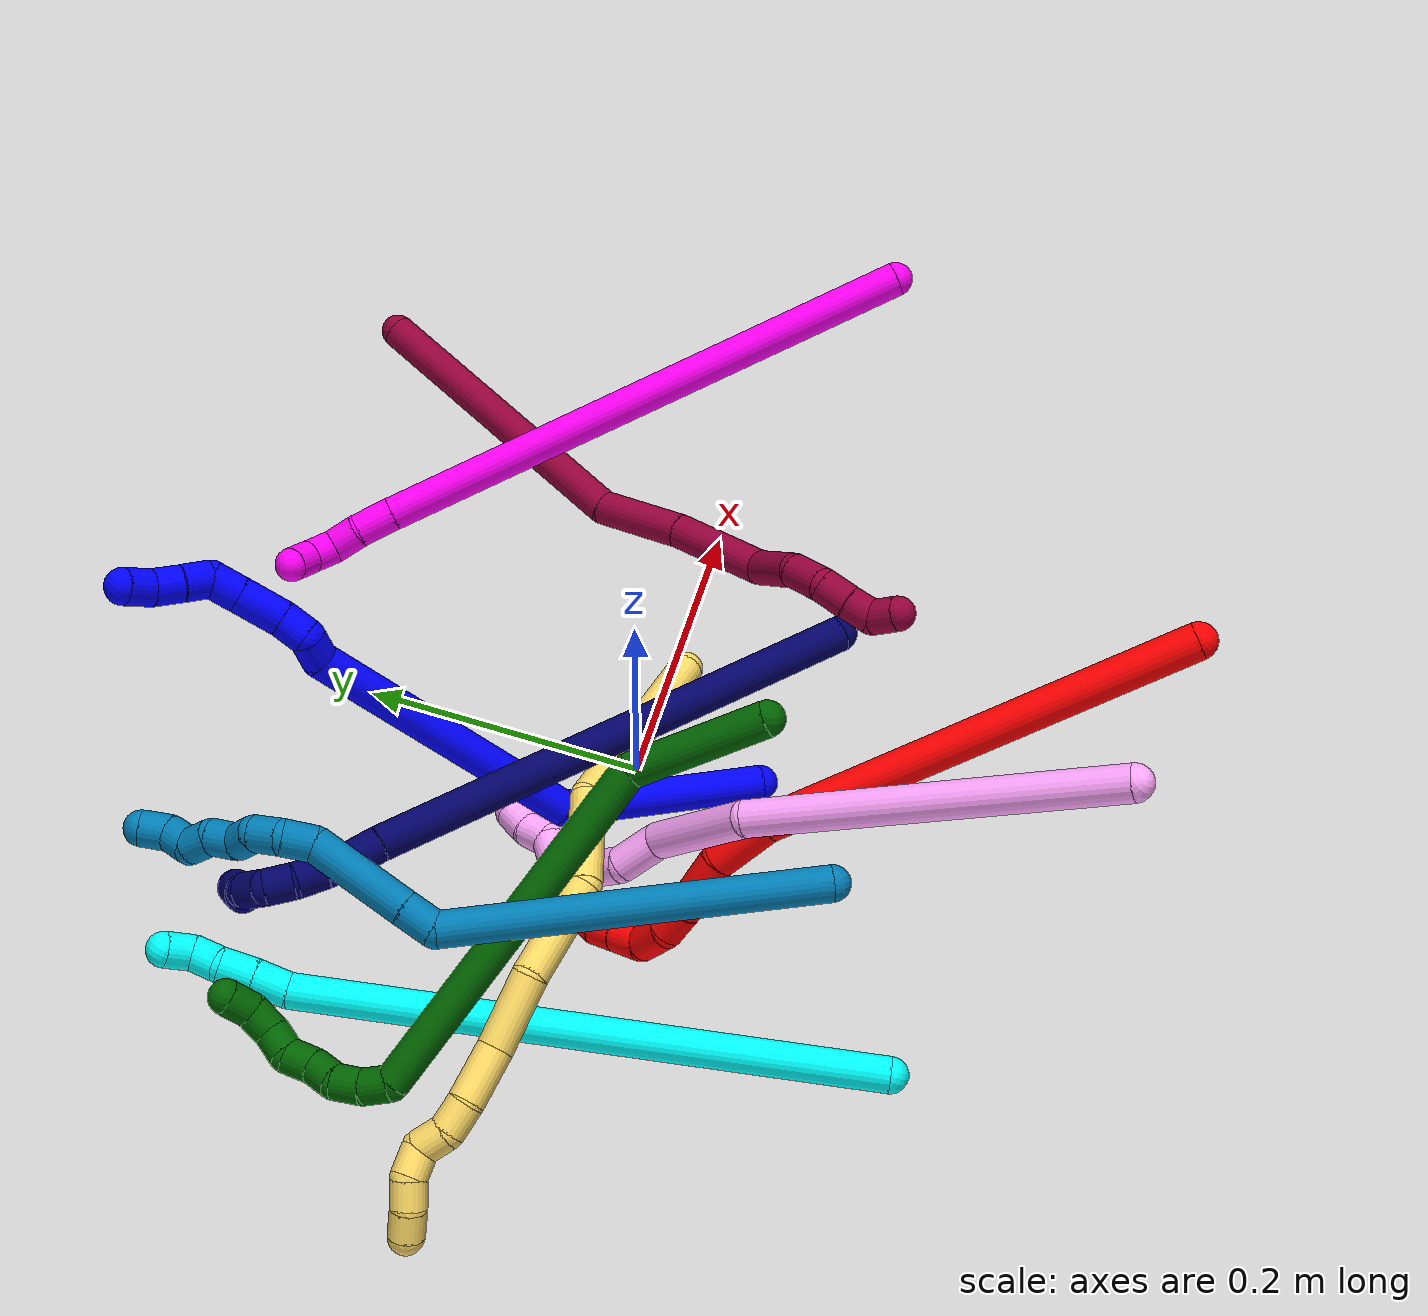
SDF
<sdf version="1.7">
 <world name="default">
  <plugin name="TubeGeneratorPlugin" filename="libtube_generator_plugin.so"/>
  <model name="photoneo_s_sensor">
   <static>1</static>
   <pose>0 0 2 1.57079 1.57079 3.14159</pose>
   <link name="link">
    <inertial><mass>0.1</mass></inertial>
    <sensor name="sensor" type="depth">
     <update_rate>30</update_rate>
     <camera>
      <horizontal_fov>1.22</horizontal_fov>
      <image><width>1920</width><height>1200</height><format>B8G8R8</format></image>
      <clip><near>0.1</near><far>4</far></clip>
      <depth_camera><output>points</output></depth_camera>
     </camera>
     <plugin name="camera_plugin" filename="libgazebo_ros_depth_camera.so">
      <baseline>0.2</baseline>
      <alwaysOn>1</alwaysOn>
      <updateRate>0.0</updateRate>
      <cameraName>camera_ir</cameraName>
      <imageTopicName>/camera/color/image_raw</imageTopicName>
      <cameraInfoTopicName>/camera/color/camera_info</cameraInfoTopicName>
      <depthImageTopicName>/camera/depth/image_raw</depthImageTopicName>
      <depthImageCameraInfoTopicName>/camera/depth/camera_info</depthImageCameraInfoTopicName>
      <pointCloudTopicName>/camera/depth/points</pointCloudTopicName>
      <frameName>fr_optical</frameName>
      <pointCloudCutoff>0.1</pointCloudCutoff>
      <pointCloudCutoffMax>2.0</pointCloudCutoffMax>
      <distortionK1>0</distortionK1>
      <distortionK2>0</distortionK2>
      <distortionK3>0</distortionK3>
      <distortionT1>0</distortionT1>
      <distortionT2>0</distortionT2>
      <CxPrime>0</CxPrime>
      <Cx>0</Cx>
      <Cy>0</Cy>
      <focalLength>0</focalLength>
      <hackBaseline>0</hackBaseline>
     </plugin>
    </sensor>
   </link>
  </model>
  <gravity>0 0 -9.8</gravity>
  <magnetic_field>6e-06 2.3e-05 -4.2e-05</magnetic_field>
  <atmosphere type="adiabatic"/>
  <physics name="default_physics" default="0" type="ode">
   <max_step_size>0.003</max_step_size>
   <real_time_factor>1</real_time_factor>
   <real_time_update_rate>1000</real_time_update_rate>
   <max_contacts>10000</max_contacts>
   <ode>
    <solver>
     <type>quick</type>
     <iters>100</iters>
     <sor>1.3</sor>
     <use_dynamic_moi_rescaling>0</use_dynamic_moi_rescaling>
    </solver>
    <constraints>
     <contact_max_correcting_vel>0</contact_max_correcting_vel>
     <contact_surface_layer>0.001</contact_surface_layer>
     <cfm>0</cfm>
     <erp>0.2</erp>
    </constraints>
   </ode>
  </physics>
  <scene><ambient>0.4 0.4 0.4 1</ambient><background>0.7 0.7 0.7 1</background><shadows>0</shadows></scene>
  <audio><device>default</device></audio>
  <spherical_coordinates>
   <surface_model>EARTH_WGS84</surface_model>
   <latitude_deg>0</latitude_deg>
   <longitude_deg>0</longitude_deg>
   <elevation>0</elevation>
   <heading_deg>0</heading_deg>
  </spherical_coordinates>
  <model name="bin">
   <static>1</static>
   <link name="bottom">
    <collision name="collision-bottom">
     <pose>0 0 -0.01 0 -0 0</pose>
     <geometry><box><size>0.8 0.6 0.02</size></box></geometry>
     <surface>
      <friction><ode><mu>100</mu><mu2>100</mu2></ode></friction>
      <contact><collide_bitmask>65535</collide_bitmask></contact>
     </surface>
    </collision>
   </link>
   <link name="west_wall">
    <collision name="collision-west_wall">
     <pose>-0.41 0 0.1 0 -0 0</pose>
     <geometry><box><size>0.02 0.6 0.2</size></box></geometry>
     <surface>
      <friction><ode><mu>100</mu><mu2>100</mu2></ode></friction>
      <contact><collide_bitmask>65535</collide_bitmask></contact>
     </surface>
    </collision>
   </link>
   <link name="east_wall">
    <collision name="collision-east_wall">
     <pose>0.41 0 0.1 0 -0 0</pose>
     <geometry><box><size>0.02 0.6 0.2</size></box></geometry>
     <surface>
      <friction><ode><mu>100</mu><mu2>100</mu2></ode></friction>
      <contact><collide_bitmask>65535</collide_bitmask></contact>
     </surface>
    </collision>
   </link>
   <link name="south_wall">
    <collision name="collision-south_wall">
     <pose>0 -0.31 0.1 0 -0 0</pose>
     <geometry><box><size>0.8 0.02 0.2</size></box></geometry>
     <surface>
      <friction><ode><mu>100</mu><mu2>100</mu2></ode></friction>
      <contact><collide_bitmask>65535</collide_bitmask></contact>
     </surface>
    </collision>
   </link>
   <link name="north_wall">
    <collision name="collision-north_wall">
     <pose>0 0.31 0.1 0 -0 0</pose>
     <geometry><box><size>0.8 0.02 0.2</size></box></geometry>
     <surface>
      <friction><ode><mu>100</mu><mu2>100</mu2></ode></friction>
      <contact><collide_bitmask>65535</collide_bitmask></contact>
     </surface>
    </collision>
   </link>
  </model>
  <model name="1">
   <static>0</static>
   <link name="1">
    <collision name="collision-cylinder-e_1_1_4">
     <pose>-0.01716 0.062226 -0.028675 -2.00262 -0.245408 0.380577</pose>
     <geometry><cylinder><radius>0.0125</radius><length>0.141263</length></cylinder></geometry>
     <surface>
      <friction><ode><mu>1.16</mu><mu2>1.16</mu2><slip1>0</slip1><slip2>0</slip2></ode></friction>
      <contact><ode><kp>1e+06</kp><kd>1</kd><max_vel>0</max_vel><min_depth>0.001</min_depth></ode></contact>
     </surface>
    </collision>
    <visual name="visual-cylinder-e_1_1_4">
     <pose>-0.01716 0.062226 -0.028675 -2.00262 -0.245408 0.380577</pose>
     <geometry><cylinder><radius>0.0125</radius><length>0.141263</length></cylinder></geometry>
     <material><ambient>0 0 1 1</ambient></material>
    </visual>
    <collision name="collision-cylinder-e_2_4_5">
     <pose>-0.033466 0.224662 -0.037266 -1.37299 0.00836 -0.006851</pose>
     <geometry><cylinder><radius>0.0125</radius><length>0.204415</length></cylinder></geometry>
     <surface>
      <friction><ode><mu>1.16</mu><mu2>1.16</mu2><slip1>0</slip1><slip2>0</slip2></ode></friction>
      <contact><ode><kp>1e+06</kp><kd>1</kd><max_vel>0</max_vel><min_depth>0.001</min_depth></ode></contact>
     </surface>
    </collision>
    <visual name="visual-cylinder-e_2_4_5">
     <pose>-0.033466 0.224662 -0.037266 -1.37299 0.00836 -0.006851</pose>
     <geometry><cylinder><radius>0.0125</radius><length>0.204415</length></cylinder></geometry>
     <material><ambient>0 0 1 1</ambient></material>
    </visual>
    <collision name="collision-cylinder-e_3_5_6">
     <pose>-0.033158 0.332414 -0.01026 -0.828251 -0.053417 0.023484</pose>
     <geometry><cylinder><radius>0.0125</radius><length>0.020499</length></cylinder></geometry>
     <surface>
      <friction><ode><mu>1.16</mu><mu2>1.16</mu2><slip1>0</slip1><slip2>0</slip2></ode></friction>
      <contact><ode><kp>1e+06</kp><kd>1</kd><max_vel>0</max_vel><min_depth>0.001</min_depth></ode></contact>
     </surface>
    </collision>
    <visual name="visual-cylinder-e_3_5_6">
     <pose>-0.033158 0.332414 -0.01026 -0.828251 -0.053417 0.023484</pose>
     <geometry><cylinder><radius>0.0125</radius><length>0.020499</length></cylinder></geometry>
     <material><ambient>0 0 1 1</ambient></material>
    </visual>
    <collision name="collision-cylinder-e_4_6_7">
     <pose>-0.030192 0.349447 -0.002599 -1.49297 0.353534 -0.327528</pose>
     <geometry><cylinder><radius>0.0125</radius><length>0.020297</length></cylinder></geometry>
     <surface>
      <friction><ode><mu>1.16</mu><mu2>1.16</mu2><slip1>0</slip1><slip2>0</slip2></ode></friction>
      <contact><ode><kp>1e+06</kp><kd>1</kd><max_vel>0</max_vel><min_depth>0.001</min_depth></ode></contact>
     </surface>
    </collision>
    <visual name="visual-cylinder-e_4_6_7">
     <pose>-0.030192 0.349447 -0.002599 -1.49297 0.353534 -0.327528</pose>
     <geometry><cylinder><radius>0.0125</radius><length>0.020297</length></cylinder></geometry>
     <material><ambient>0 0 1 1</ambient></material>
    </visual>
    <collision name="collision-cylinder-e_5_7_8">
     <pose>-0.024049 0.37468 -0.001118 -1.52379 0.165334 -0.157771</pose>
     <geometry><cylinder><radius>0.0125</radius><length>0.031954</length></cylinder></geometry>
     <surface>
      <friction><ode><mu>1.16</mu><mu2>1.16</mu2><slip1>0</slip1><slip2>0</slip2></ode></friction>
      <contact><ode><kp>1e+06</kp><kd>1</kd><max_vel>0</max_vel><min_depth>0.001</min_depth></ode></contact>
     </surface>
    </collision>
    <visual name="visual-cylinder-e_5_7_8">
     <pose>-0.024049 0.37468 -0.001118 -1.52379 0.165334 -0.157771</pose>
     <geometry><cylinder><radius>0.0125</radius><length>0.031954</length></cylinder></geometry>
     <material><ambient>0 0 1 1</ambient></material>
    </visual>
    <collision name="collision-cylinder-e_6_8_9">
     <pose>-0.019703 0.400833 4e-05 -1.53071 0.163318 -0.156926</pose>
     <geometry><cylinder><radius>0.0125</radius><length>0.021118</length></cylinder></geometry>
     <surface>
      <friction><ode><mu>1.16</mu><mu2>1.16</mu2><slip1>0</slip1><slip2>0</slip2></ode></friction>
      <contact><ode><kp>1e+06</kp><kd>1</kd><max_vel>0</max_vel><min_depth>0.001</min_depth></ode></contact>
     </surface>
    </collision>
    <visual name="visual-cylinder-e_6_8_9">
     <pose>-0.019703 0.400833 4e-05 -1.53071 0.163318 -0.156926</pose>
     <geometry><cylinder><radius>0.0125</radius><length>0.021118</length></cylinder></geometry>
     <material><ambient>0 0 1 1</ambient></material>
    </visual>
    <collision name="collision-cylinder-e_7_9_10">
     <pose>-0.022511 0.419714 -0.002431 -1.89943 -0.468125 0.6433</pose>
     <geometry><cylinder><radius>0.0125</radius><length>0.020059</length></cylinder></geometry>
     <surface>
      <friction><ode><mu>1.16</mu><mu2>1.16</mu2><slip1>0</slip1><slip2>0</slip2></ode></friction>
      <contact><ode><kp>1e+06</kp><kd>1</kd><max_vel>0</max_vel><min_depth>0.001</min_depth></ode></contact>
     </surface>
    </collision>
    <visual name="visual-cylinder-e_7_9_10">
     <pose>-0.022511 0.419714 -0.002431 -1.89943 -0.468125 0.6433</pose>
     <geometry><cylinder><radius>0.0125</radius><length>0.020059</length></cylinder></geometry>
     <material><ambient>0 0 1 1</ambient></material>
    </visual>
    <collision name="collision-cylinder-e_8_10_11">
     <pose>-0.030943 0.436825 -0.008501 -1.92358 -0.401262 0.567446</pose>
     <geometry><cylinder><radius>0.0125</radius><length>0.020002</length></cylinder></geometry>
     <surface>
      <friction><ode><mu>1.16</mu><mu2>1.16</mu2><slip1>0</slip1><slip2>0</slip2></ode></friction>
      <contact><ode><kp>1e+06</kp><kd>1</kd><max_vel>0</max_vel><min_depth>0.001</min_depth></ode></contact>
     </surface>
    </collision>
    <visual name="visual-cylinder-e_8_10_11">
     <pose>-0.030943 0.436825 -0.008501 -1.92358 -0.401262 0.567446</pose>
     <geometry><cylinder><radius>0.0125</radius><length>0.020002</length></cylinder></geometry>
     <material><ambient>0 0 1 1</ambient></material>
    </visual>
    <collision name="collision-cylinder-e_9_11_2">
     <pose>-0.039642 0.454463 -0.011839 -1.58817 -0.489348 0.49758</pose>
     <geometry><cylinder><radius>0.0125</radius><length>0.020393</length></cylinder></geometry>
     <surface>
      <friction><ode><mu>1.16</mu><mu2>1.16</mu2><slip1>0</slip1><slip2>0</slip2></ode></friction>
      <contact><ode><kp>1e+06</kp><kd>1</kd><max_vel>0</max_vel><min_depth>0.001</min_depth></ode></contact>
     </surface>
    </collision>
    <visual name="visual-cylinder-e_9_11_2">
     <pose>-0.039642 0.454463 -0.011839 -1.58817 -0.489348 0.49758</pose>
     <geometry><cylinder><radius>0.0125</radius><length>0.020393</length></cylinder></geometry>
     <material><ambient>0 0 1 1</ambient></material>
    </visual>
    <collision name="collision-sphere-2">
     <pose>-0.044435 0.463462 -0.011995 0 -0 0</pose>
     <geometry><sphere><radius>0.0125</radius></sphere></geometry>
     <surface>
      <friction><ode><mu>1.16</mu><mu2>1.16</mu2><slip1>0</slip1><slip2>0</slip2></ode></friction>
      <contact><ode><kp>1e+06</kp><kd>1</kd><max_vel>0</max_vel><min_depth>0.001</min_depth></ode></contact>
     </surface>
    </collision>
    <visual name="visual-sphere-2">
     <pose>-0.044435 0.463462 -0.011995 0 -0 0</pose>
     <geometry><sphere><radius>0.0125</radius></sphere></geometry>
     <material><ambient>0 0 1 1</ambient></material>
    </visual>
    <collision name="collision-sphere-11">
     <pose>-0.034849 0.445465 -0.011682 0 -0 0</pose>
     <geometry><sphere><radius>0.0125</radius></sphere></geometry>
     <surface>
      <friction><ode><mu>1.16</mu><mu2>1.16</mu2><slip1>0</slip1><slip2>0</slip2></ode></friction>
      <contact><ode><kp>1e+06</kp><kd>1</kd><max_vel>0</max_vel><min_depth>0.001</min_depth></ode></contact>
     </surface>
    </collision>
    <visual name="visual-sphere-11">
     <pose>-0.034849 0.445465 -0.011682 0 -0 0</pose>
     <geometry><sphere><radius>0.0125</radius></sphere></geometry>
     <material><ambient>0 0 1 1</ambient></material>
    </visual>
    <collision name="collision-sphere-10">
     <pose>-0.027037 0.428186 -0.00532 0 -0 0</pose>
     <geometry><sphere><radius>0.0125</radius></sphere></geometry>
     <surface>
      <friction><ode><mu>1.16</mu><mu2>1.16</mu2><slip1>0</slip1><slip2>0</slip2></ode></friction>
      <contact><ode><kp>1e+06</kp><kd>1</kd><max_vel>0</max_vel><min_depth>0.001</min_depth></ode></contact>
     </surface>
    </collision>
    <visual name="visual-sphere-10">
     <pose>-0.027037 0.428186 -0.00532 0 -0 0</pose>
     <geometry><sphere><radius>0.0125</radius></sphere></geometry>
     <material><ambient>0 0 1 1</ambient></material>
    </visual>
    <collision name="collision-sphere-9">
     <pose>-0.017986 0.411243 0.000457 0 -0 0</pose>
     <geometry><sphere><radius>0.0125</radius></sphere></geometry>
     <surface>
      <friction><ode><mu>1.16</mu><mu2>1.16</mu2><slip1>0</slip1><slip2>0</slip2></ode></friction>
      <contact><ode><kp>1e+06</kp><kd>1</kd><max_vel>0</max_vel><min_depth>0.001</min_depth></ode></contact>
     </surface>
    </collision>
    <visual name="visual-sphere-9">
     <pose>-0.017986 0.411243 0.000457 0 -0 0</pose>
     <geometry><sphere><radius>0.0125</radius></sphere></geometry>
     <material><ambient>0 0 1 1</ambient></material>
    </visual>
    <collision name="collision-sphere-4">
     <pose>-0.03432 0.124452 -0.057351 0 -0 0</pose>
     <geometry><sphere><radius>0.0125</radius></sphere></geometry>
     <surface>
      <friction><ode><mu>1.16</mu><mu2>1.16</mu2><slip1>0</slip1><slip2>0</slip2></ode></friction>
      <contact><ode><kp>1e+06</kp><kd>1</kd><max_vel>0</max_vel><min_depth>0.001</min_depth></ode></contact>
     </surface>
    </collision>
    <visual name="visual-sphere-4">
     <pose>-0.03432 0.124452 -0.057351 0 -0 0</pose>
     <geometry><sphere><radius>0.0125</radius></sphere></geometry>
     <material><ambient>0 0 1 1</ambient></material>
    </visual>
    <collision name="collision-sphere-1">
     <geometry><sphere><radius>0.0125</radius></sphere></geometry>
     <surface>
      <friction><ode><mu>1.16</mu><mu2>1.16</mu2><slip1>0</slip1><slip2>0</slip2></ode></friction>
      <contact><ode><kp>1e+06</kp><kd>1</kd><max_vel>0</max_vel><min_depth>0.001</min_depth></ode></contact>
     </surface>
    </collision>
    <visual name="visual-sphere-1">
     <geometry><sphere><radius>0.0125</radius></sphere></geometry>
     <material><ambient>0 0 1 1</ambient></material>
    </visual>
    <collision name="collision-sphere-8">
     <pose>-0.021419 0.390422 -0.000378 0 -0 0</pose>
     <geometry><sphere><radius>0.0125</radius></sphere></geometry>
     <surface>
      <friction><ode><mu>1.16</mu><mu2>1.16</mu2><slip1>0</slip1><slip2>0</slip2></ode></friction>
      <contact><ode><kp>1e+06</kp><kd>1</kd><max_vel>0</max_vel><min_depth>0.001</min_depth></ode></contact>
     </surface>
    </collision>
    <visual name="visual-sphere-8">
     <pose>-0.021419 0.390422 -0.000378 0 -0 0</pose>
     <geometry><sphere><radius>0.0125</radius></sphere></geometry>
     <material><ambient>0 0 1 1</ambient></material>
    </visual>
    <collision name="collision-sphere-5">
     <pose>-0.032611 0.324873 -0.01718 0 -0 0</pose>
     <geometry><sphere><radius>0.0125</radius></sphere></geometry>
     <surface>
      <friction><ode><mu>1.16</mu><mu2>1.16</mu2><slip1>0</slip1><slip2>0</slip2></ode></friction>
      <contact><ode><kp>1e+06</kp><kd>1</kd><max_vel>0</max_vel><min_depth>0.001</min_depth></ode></contact>
     </surface>
    </collision>
    <visual name="visual-sphere-5">
     <pose>-0.032611 0.324873 -0.01718 0 -0 0</pose>
     <geometry><sphere><radius>0.0125</radius></sphere></geometry>
     <material><ambient>0 0 1 1</ambient></material>
    </visual>
    <collision name="collision-sphere-6">
     <pose>-0.033706 0.339955 -0.003339 0 -0 0</pose>
     <geometry><sphere><radius>0.0125</radius></sphere></geometry>
     <surface>
      <friction><ode><mu>1.16</mu><mu2>1.16</mu2><slip1>0</slip1><slip2>0</slip2></ode></friction>
      <contact><ode><kp>1e+06</kp><kd>1</kd><max_vel>0</max_vel><min_depth>0.001</min_depth></ode></contact>
     </surface>
    </collision>
    <visual name="visual-sphere-6">
     <pose>-0.033706 0.339955 -0.003339 0 -0 0</pose>
     <geometry><sphere><radius>0.0125</radius></sphere></geometry>
     <material><ambient>0 0 1 1</ambient></material>
    </visual>
    <collision name="collision-sphere-7">
     <pose>-0.026679 0.358939 -0.001859 0 -0 0</pose>
     <geometry><sphere><radius>0.0125</radius></sphere></geometry>
     <surface>
      <friction><ode><mu>1.16</mu><mu2>1.16</mu2><slip1>0</slip1><slip2>0</slip2></ode></friction>
      <contact><ode><kp>1e+06</kp><kd>1</kd><max_vel>0</max_vel><min_depth>0.001</min_depth></ode></contact>
     </surface>
    </collision>
    <visual name="visual-sphere-7">
     <pose>-0.026679 0.358939 -0.001859 0 -0 0</pose>
     <geometry><sphere><radius>0.0125</radius></sphere></geometry>
     <material><ambient>0 0 1 1</ambient></material>
    </visual>
    <inertial>
     <pose>-0.027242 0.230966 -0.024853 0 -0 0</pose>
     <mass>0.5</mass>
     <inertia>
      <ixx>0.001027</ixx>
      <ixy>0</ixy>
      <ixz>0</ixz>
      <iyy>0.000188</iyy>
      <iyz>0</iyz>
      <izz>-0.000877</izz>
     </inertia>
    </inertial>
   </link>
   <pose>0.00779 -0.088176 0.017669 0.491979 0.424287 0.330554</pose>
  </model>
  <model name="2">
   <static>0</static>
   <link name="2">
    <collision name="collision-cylinder-e_1_1_4">
     <pose>-0.041145 0.048538 -0.135997 -2.79878 -0.27758 1.35794</pose>
     <geometry><cylinder><radius>0.0125</radius><length>0.300294</length></cylinder></geometry>
     <surface>
      <friction><ode><mu>1.16</mu><mu2>1.16</mu2><slip1>0</slip1><slip2>0</slip2></ode></friction>
      <contact><ode><kp>1e+06</kp><kd>1</kd><max_vel>0</max_vel><min_depth>0.001</min_depth></ode></contact>
     </surface>
    </collision>
    <visual name="visual-cylinder-e_1_1_4">
     <pose>-0.041145 0.048538 -0.135997 -2.79878 -0.27758 1.35794</pose>
     <geometry><cylinder><radius>0.0125</radius><length>0.300294</length></cylinder></geometry>
     <material><ambient>1 0 0 1</ambient></material>
    </visual>
    <collision name="collision-cylinder-e_2_4_5">
     <pose>-0.088996 0.097615 -0.292466 -3.11529 -0.316472 2.9771</pose>
     <geometry><cylinder><radius>0.0125</radius><length>0.043097</length></cylinder></geometry>
     <surface>
      <friction><ode><mu>1.16</mu><mu2>1.16</mu2><slip1>0</slip1><slip2>0</slip2></ode></friction>
      <contact><ode><kp>1e+06</kp><kd>1</kd><max_vel>0</max_vel><min_depth>0.001</min_depth></ode></contact>
     </surface>
    </collision>
    <visual name="visual-cylinder-e_2_4_5">
     <pose>-0.088996 0.097615 -0.292466 -3.11529 -0.316472 2.9771</pose>
     <geometry><cylinder><radius>0.0125</radius><length>0.043097</length></cylinder></geometry>
     <material><ambient>1 0 0 1</ambient></material>
    </visual>
    <collision name="collision-cylinder-e_3_5_6">
     <pose>-0.104742 0.092262 -0.332932 2.85507 -0.409205 -1.92666</pose>
     <geometry><cylinder><radius>0.0125</radius><length>0.04544</length></cylinder></geometry>
     <surface>
      <friction><ode><mu>1.16</mu><mu2>1.16</mu2><slip1>0</slip1><slip2>0</slip2></ode></friction>
      <contact><ode><kp>1e+06</kp><kd>1</kd><max_vel>0</max_vel><min_depth>0.001</min_depth></ode></contact>
     </surface>
    </collision>
    <visual name="visual-cylinder-e_3_5_6">
     <pose>-0.104742 0.092262 -0.332932 2.85507 -0.409205 -1.92666</pose>
     <geometry><cylinder><radius>0.0125</radius><length>0.04544</length></cylinder></geometry>
     <material><ambient>1 0 0 1</ambient></material>
    </visual>
    <collision name="collision-cylinder-e_4_6_7">
     <pose>-0.117583 0.084042 -0.36287 2.91145 -0.356357 -2.00041</pose>
     <geometry><cylinder><radius>0.0125</radius><length>0.021795</length></cylinder></geometry>
     <surface>
      <friction><ode><mu>1.16</mu><mu2>1.16</mu2><slip1>0</slip1><slip2>0</slip2></ode></friction>
      <contact><ode><kp>1e+06</kp><kd>1</kd><max_vel>0</max_vel><min_depth>0.001</min_depth></ode></contact>
     </surface>
    </collision>
    <visual name="visual-cylinder-e_4_6_7">
     <pose>-0.117583 0.084042 -0.36287 2.91145 -0.356357 -2.00041</pose>
     <geometry><cylinder><radius>0.0125</radius><length>0.021795</length></cylinder></geometry>
     <material><ambient>1 0 0 1</ambient></material>
    </visual>
    <collision name="collision-cylinder-e_5_7_8">
     <pose>-0.12054 0.07869 -0.386181 2.91926 0.061577 0.538406</pose>
     <geometry><cylinder><radius>0.0125</radius><length>0.027463</length></cylinder></geometry>
     <surface>
      <friction><ode><mu>1.16</mu><mu2>1.16</mu2><slip1>0</slip1><slip2>0</slip2></ode></friction>
      <contact><ode><kp>1e+06</kp><kd>1</kd><max_vel>0</max_vel><min_depth>0.001</min_depth></ode></contact>
     </surface>
    </collision>
    <visual name="visual-cylinder-e_5_7_8">
     <pose>-0.12054 0.07869 -0.386181 2.91926 0.061577 0.538406</pose>
     <geometry><cylinder><radius>0.0125</radius><length>0.027463</length></cylinder></geometry>
     <material><ambient>1 0 0 1</ambient></material>
    </visual>
    <collision name="collision-cylinder-e_6_8_9">
     <pose>-0.114555 0.078384 -0.40863 -2.85091 0.49689 -2.09493</pose>
     <geometry><cylinder><radius>0.0125</radius><length>0.021565</length></cylinder></geometry>
     <surface>
      <friction><ode><mu>1.16</mu><mu2>1.16</mu2><slip1>0</slip1><slip2>0</slip2></ode></friction>
      <contact><ode><kp>1e+06</kp><kd>1</kd><max_vel>0</max_vel><min_depth>0.001</min_depth></ode></contact>
     </surface>
    </collision>
    <visual name="visual-cylinder-e_6_8_9">
     <pose>-0.114555 0.078384 -0.40863 -2.85091 0.49689 -2.09493</pose>
     <geometry><cylinder><radius>0.0125</radius><length>0.021565</length></cylinder></geometry>
     <material><ambient>1 0 0 1</ambient></material>
    </visual>
    <collision name="collision-cylinder-e_7_9_10">
     <pose>-0.104526 0.083137 -0.426276 -2.90824 0.506941 -2.29178</pose>
     <geometry><cylinder><radius>0.0125</radius><length>0.02014</length></cylinder></geometry>
     <surface>
      <friction><ode><mu>1.16</mu><mu2>1.16</mu2><slip1>0</slip1><slip2>0</slip2></ode></friction>
      <contact><ode><kp>1e+06</kp><kd>1</kd><max_vel>0</max_vel><min_depth>0.001</min_depth></ode></contact>
     </surface>
    </collision>
    <visual name="visual-cylinder-e_7_9_10">
     <pose>-0.104526 0.083137 -0.426276 -2.90824 0.506941 -2.29178</pose>
     <geometry><cylinder><radius>0.0125</radius><length>0.02014</length></cylinder></geometry>
     <material><ambient>1 0 0 1</ambient></material>
    </visual>
    <collision name="collision-cylinder-e_8_10_2">
     <pose>-0.093223 0.091677 -0.439157 -2.15672 0.68779 -1.17716</pose>
     <geometry><cylinder><radius>0.0125</radius><length>0.020207</length></cylinder></geometry>
     <surface>
      <friction><ode><mu>1.16</mu><mu2>1.16</mu2><slip1>0</slip1><slip2>0</slip2></ode></friction>
      <contact><ode><kp>1e+06</kp><kd>1</kd><max_vel>0</max_vel><min_depth>0.001</min_depth></ode></contact>
     </surface>
    </collision>
    <visual name="visual-cylinder-e_8_10_2">
     <pose>-0.093223 0.091677 -0.439157 -2.15672 0.68779 -1.17716</pose>
     <geometry><cylinder><radius>0.0125</radius><length>0.020207</length></cylinder></geometry>
     <material><ambient>1 0 0 1</ambient></material>
    </visual>
    <collision name="collision-sphere-2">
     <pose>-0.086809 0.098181 -0.443474 0 -0 0</pose>
     <geometry><sphere><radius>0.0125</radius></sphere></geometry>
     <surface>
      <friction><ode><mu>1.16</mu><mu2>1.16</mu2><slip1>0</slip1><slip2>0</slip2></ode></friction>
      <contact><ode><kp>1e+06</kp><kd>1</kd><max_vel>0</max_vel><min_depth>0.001</min_depth></ode></contact>
     </surface>
    </collision>
    <visual name="visual-sphere-2">
     <pose>-0.086809 0.098181 -0.443474 0 -0 0</pose>
     <geometry><sphere><radius>0.0125</radius></sphere></geometry>
     <material><ambient>1 0 0 1</ambient></material>
    </visual>
    <collision name="collision-sphere-10">
     <pose>-0.099637 0.085172 -0.434841 0 -0 0</pose>
     <geometry><sphere><radius>0.0125</radius></sphere></geometry>
     <surface>
      <friction><ode><mu>1.16</mu><mu2>1.16</mu2><slip1>0</slip1><slip2>0</slip2></ode></friction>
      <contact><ode><kp>1e+06</kp><kd>1</kd><max_vel>0</max_vel><min_depth>0.001</min_depth></ode></contact>
     </surface>
    </collision>
    <visual name="visual-sphere-10">
     <pose>-0.099637 0.085172 -0.434841 0 -0 0</pose>
     <geometry><sphere><radius>0.0125</radius></sphere></geometry>
     <material><ambient>1 0 0 1</ambient></material>
    </visual>
    <collision name="collision-sphere-9">
     <pose>-0.109415 0.081101 -0.417711 0 -0 0</pose>
     <geometry><sphere><radius>0.0125</radius></sphere></geometry>
     <surface>
      <friction><ode><mu>1.16</mu><mu2>1.16</mu2><slip1>0</slip1><slip2>0</slip2></ode></friction>
      <contact><ode><kp>1e+06</kp><kd>1</kd><max_vel>0</max_vel><min_depth>0.001</min_depth></ode></contact>
     </surface>
    </collision>
    <visual name="visual-sphere-9">
     <pose>-0.109415 0.081101 -0.417711 0 -0 0</pose>
     <geometry><sphere><radius>0.0125</radius></sphere></geometry>
     <material><ambient>1 0 0 1</ambient></material>
    </visual>
    <collision name="collision-sphere-4">
     <pose>-0.082289 0.097076 -0.271995 0 -0 0</pose>
     <geometry><sphere><radius>0.0125</radius></sphere></geometry>
     <surface>
      <friction><ode><mu>1.16</mu><mu2>1.16</mu2><slip1>0</slip1><slip2>0</slip2></ode></friction>
      <contact><ode><kp>1e+06</kp><kd>1</kd><max_vel>0</max_vel><min_depth>0.001</min_depth></ode></contact>
     </surface>
    </collision>
    <visual name="visual-sphere-4">
     <pose>-0.082289 0.097076 -0.271995 0 -0 0</pose>
     <geometry><sphere><radius>0.0125</radius></sphere></geometry>
     <material><ambient>1 0 0 1</ambient></material>
    </visual>
    <collision name="collision-sphere-1">
     <geometry><sphere><radius>0.0125</radius></sphere></geometry>
     <surface>
      <friction><ode><mu>1.16</mu><mu2>1.16</mu2><slip1>0</slip1><slip2>0</slip2></ode></friction>
      <contact><ode><kp>1e+06</kp><kd>1</kd><max_vel>0</max_vel><min_depth>0.001</min_depth></ode></contact>
     </surface>
    </collision>
    <visual name="visual-sphere-1">
     <geometry><sphere><radius>0.0125</radius></sphere></geometry>
     <material><ambient>1 0 0 1</ambient></material>
    </visual>
    <collision name="collision-sphere-8">
     <pose>-0.119695 0.075668 -0.399549 0 -0 0</pose>
     <geometry><sphere><radius>0.0125</radius></sphere></geometry>
     <surface>
      <friction><ode><mu>1.16</mu><mu2>1.16</mu2><slip1>0</slip1><slip2>0</slip2></ode></friction>
      <contact><ode><kp>1e+06</kp><kd>1</kd><max_vel>0</max_vel><min_depth>0.001</min_depth></ode></contact>
     </surface>
    </collision>
    <visual name="visual-sphere-8">
     <pose>-0.119695 0.075668 -0.399549 0 -0 0</pose>
     <geometry><sphere><radius>0.0125</radius></sphere></geometry>
     <material><ambient>1 0 0 1</ambient></material>
    </visual>
    <collision name="collision-sphere-5">
     <pose>-0.095702 0.098153 -0.312937 0 -0 0</pose>
     <geometry><sphere><radius>0.0125</radius></sphere></geometry>
     <surface>
      <friction><ode><mu>1.16</mu><mu2>1.16</mu2><slip1>0</slip1><slip2>0</slip2></ode></friction>
      <contact><ode><kp>1e+06</kp><kd>1</kd><max_vel>0</max_vel><min_depth>0.001</min_depth></ode></contact>
     </surface>
    </collision>
    <visual name="visual-sphere-5">
     <pose>-0.095702 0.098153 -0.312937 0 -0 0</pose>
     <geometry><sphere><radius>0.0125</radius></sphere></geometry>
     <material><ambient>1 0 0 1</ambient></material>
    </visual>
    <collision name="collision-sphere-6">
     <pose>-0.113782 0.086371 -0.352926 0 -0 0</pose>
     <geometry><sphere><radius>0.0125</radius></sphere></geometry>
     <surface>
      <friction><ode><mu>1.16</mu><mu2>1.16</mu2><slip1>0</slip1><slip2>0</slip2></ode></friction>
      <contact><ode><kp>1e+06</kp><kd>1</kd><max_vel>0</max_vel><min_depth>0.001</min_depth></ode></contact>
     </surface>
    </collision>
    <visual name="visual-sphere-6">
     <pose>-0.113782 0.086371 -0.352926 0 -0 0</pose>
     <geometry><sphere><radius>0.0125</radius></sphere></geometry>
     <material><ambient>1 0 0 1</ambient></material>
    </visual>
    <collision name="collision-sphere-7">
     <pose>-0.121385 0.081712 -0.372813 0 -0 0</pose>
     <geometry><sphere><radius>0.0125</radius></sphere></geometry>
     <surface>
      <friction><ode><mu>1.16</mu><mu2>1.16</mu2><slip1>0</slip1><slip2>0</slip2></ode></friction>
      <contact><ode><kp>1e+06</kp><kd>1</kd><max_vel>0</max_vel><min_depth>0.001</min_depth></ode></contact>
     </surface>
    </collision>
    <visual name="visual-sphere-7">
     <pose>-0.121385 0.081712 -0.372813 0 -0 0</pose>
     <geometry><sphere><radius>0.0125</radius></sphere></geometry>
     <material><ambient>1 0 0 1</ambient></material>
    </visual>
    <inertial>
     <pose>-0.066565 0.06437 -0.226715 0 -0 0</pose>
     <mass>0.5</mass>
     <inertia>
      <ixx>0.002566</ixx>
      <ixy>0</ixy>
      <ixz>0</ixz>
      <iyy>0.001896</iyy>
      <iyz>0</iyz>
      <izz>-0.00014</izz>
     </inertia>
    </inertial>
   </link>
   <pose>0.082512 -0.347604 0.234108 0.828165 0.079905 0.260258</pose>
  </model>
  <model name="3">
   <static>0</static>
   <link name="3">
    <collision name="collision-cylinder-e_1_1_4">
     <pose>0.010489 0.190423 0.073465 -1.20259 0.051345 -0.035229</pose>
     <geometry><cylinder><radius>0.0125</radius><length>0.408744</length></cylinder></geometry>
     <surface>
      <friction><ode><mu>1.16</mu><mu2>1.16</mu2><slip1>0</slip1><slip2>0</slip2></ode></friction>
      <contact><ode><kp>1e+06</kp><kd>1</kd><max_vel>0</max_vel><min_depth>0.001</min_depth></ode></contact>
     </surface>
    </collision>
    <visual name="visual-cylinder-e_1_1_4">
     <pose>0.010489 0.190423 0.073465 -1.20259 0.051345 -0.035229</pose>
     <geometry><cylinder><radius>0.0125</radius><length>0.408744</length></cylinder></geometry>
     <material><ambient>0.003922 1 0.996078 1</ambient></material>
    </visual>
    <collision name="collision-cylinder-e_2_4_5">
     <pose>0.022281 0.393508 0.147971 -1.48882 0.102191 -0.094152</pose>
     <geometry><cylinder><radius>0.0125</radius><length>0.025544</length></cylinder></geometry>
     <surface>
      <friction><ode><mu>1.16</mu><mu2>1.16</mu2><slip1>0</slip1><slip2>0</slip2></ode></friction>
      <contact><ode><kp>1e+06</kp><kd>1</kd><max_vel>0</max_vel><min_depth>0.001</min_depth></ode></contact>
     </surface>
    </collision>
    <visual name="visual-cylinder-e_2_4_5">
     <pose>0.022281 0.393508 0.147971 -1.48882 0.102191 -0.094152</pose>
     <geometry><cylinder><radius>0.0125</radius><length>0.025544</length></cylinder></geometry>
     <material><ambient>0.003922 1 0.996078 1</ambient></material>
    </visual>
    <collision name="collision-cylinder-e_3_5_6">
     <pose>0.02579 0.418135 0.150514 -1.44586 0.181021 -0.159805</pose>
     <geometry><cylinder><radius>0.0125</radius><length>0.024516</length></cylinder></geometry>
     <surface>
      <friction><ode><mu>1.16</mu><mu2>1.16</mu2><slip1>0</slip1><slip2>0</slip2></ode></friction>
      <contact><ode><kp>1e+06</kp><kd>1</kd><max_vel>0</max_vel><min_depth>0.001</min_depth></ode></contact>
     </surface>
    </collision>
    <visual name="visual-cylinder-e_3_5_6">
     <pose>0.02579 0.418135 0.150514 -1.44586 0.181021 -0.159805</pose>
     <geometry><cylinder><radius>0.0125</radius><length>0.024516</length></cylinder></geometry>
     <material><ambient>0.003922 1 0.996078 1</ambient></material>
    </visual>
    <collision name="collision-cylinder-e_4_6_7">
     <pose>0.025843 0.439979 0.153786 -1.39352 -0.211477 0.177154</pose>
     <geometry><cylinder><radius>0.0125</radius><length>0.020532</length></cylinder></geometry>
     <surface>
      <friction><ode><mu>1.16</mu><mu2>1.16</mu2><slip1>0</slip1><slip2>0</slip2></ode></friction>
      <contact><ode><kp>1e+06</kp><kd>1</kd><max_vel>0</max_vel><min_depth>0.001</min_depth></ode></contact>
     </surface>
    </collision>
    <visual name="visual-cylinder-e_4_6_7">
     <pose>0.025843 0.439979 0.153786 -1.39352 -0.211477 0.177154</pose>
     <geometry><cylinder><radius>0.0125</radius><length>0.020532</length></cylinder></geometry>
     <material><ambient>0.003922 1 0.996078 1</ambient></material>
    </visual>
    <collision name="collision-cylinder-e_5_7_2">
     <pose>0.02897 0.458527 0.157479 -1.35247 0.536656 -0.434324</pose>
     <geometry><cylinder><radius>0.0125</radius><length>0.020664</length></cylinder></geometry>
     <surface>
      <friction><ode><mu>1.16</mu><mu2>1.16</mu2><slip1>0</slip1><slip2>0</slip2></ode></friction>
      <contact><ode><kp>1e+06</kp><kd>1</kd><max_vel>0</max_vel><min_depth>0.001</min_depth></ode></contact>
     </surface>
    </collision>
    <visual name="visual-cylinder-e_5_7_2">
     <pose>0.02897 0.458527 0.157479 -1.35247 0.536656 -0.434324</pose>
     <geometry><cylinder><radius>0.0125</radius><length>0.020664</length></cylinder></geometry>
     <material><ambient>0.003922 1 0.996078 1</ambient></material>
    </visual>
    <collision name="collision-sphere-2">
     <pose>0.034252 0.467196 0.159403 0 -0 0</pose>
     <geometry><sphere><radius>0.0125</radius></sphere></geometry>
     <surface>
      <friction><ode><mu>1.16</mu><mu2>1.16</mu2><slip1>0</slip1><slip2>0</slip2></ode></friction>
      <contact><ode><kp>1e+06</kp><kd>1</kd><max_vel>0</max_vel><min_depth>0.001</min_depth></ode></contact>
     </surface>
    </collision>
    <visual name="visual-sphere-2">
     <pose>0.034252 0.467196 0.159403 0 -0 0</pose>
     <geometry><sphere><radius>0.0125</radius></sphere></geometry>
     <material><ambient>0.003922 1 0.996078 1</ambient></material>
    </visual>
    <collision name="collision-sphere-7">
     <pose>0.023688 0.449858 0.155556 0 -0 0</pose>
     <geometry><sphere><radius>0.0125</radius></sphere></geometry>
     <surface>
      <friction><ode><mu>1.16</mu><mu2>1.16</mu2><slip1>0</slip1><slip2>0</slip2></ode></friction>
      <contact><ode><kp>1e+06</kp><kd>1</kd><max_vel>0</max_vel><min_depth>0.001</min_depth></ode></contact>
     </surface>
    </collision>
    <visual name="visual-sphere-7">
     <pose>0.023688 0.449858 0.155556 0 -0 0</pose>
     <geometry><sphere><radius>0.0125</radius></sphere></geometry>
     <material><ambient>0.003922 1 0.996078 1</ambient></material>
    </visual>
    <collision name="collision-sphere-6">
     <pose>0.027997 0.430099 0.152016 0 -0 0</pose>
     <geometry><sphere><radius>0.0125</radius></sphere></geometry>
     <surface>
      <friction><ode><mu>1.16</mu><mu2>1.16</mu2><slip1>0</slip1><slip2>0</slip2></ode></friction>
      <contact><ode><kp>1e+06</kp><kd>1</kd><max_vel>0</max_vel><min_depth>0.001</min_depth></ode></contact>
     </surface>
    </collision>
    <visual name="visual-sphere-6">
     <pose>0.027997 0.430099 0.152016 0 -0 0</pose>
     <geometry><sphere><radius>0.0125</radius></sphere></geometry>
     <material><ambient>0.003922 1 0.996078 1</ambient></material>
    </visual>
    <collision name="collision-sphere-5">
     <pose>0.023584 0.406171 0.149011 0 -0 0</pose>
     <geometry><sphere><radius>0.0125</radius></sphere></geometry>
     <surface>
      <friction><ode><mu>1.16</mu><mu2>1.16</mu2><slip1>0</slip1><slip2>0</slip2></ode></friction>
      <contact><ode><kp>1e+06</kp><kd>1</kd><max_vel>0</max_vel><min_depth>0.001</min_depth></ode></contact>
     </surface>
    </collision>
    <visual name="visual-sphere-5">
     <pose>0.023584 0.406171 0.149011 0 -0 0</pose>
     <geometry><sphere><radius>0.0125</radius></sphere></geometry>
     <material><ambient>0.003922 1 0.996078 1</ambient></material>
    </visual>
    <collision name="collision-sphere-1">
     <geometry><sphere><radius>0.0125</radius></sphere></geometry>
     <surface>
      <friction><ode><mu>1.16</mu><mu2>1.16</mu2><slip1>0</slip1><slip2>0</slip2></ode></friction>
      <contact><ode><kp>1e+06</kp><kd>1</kd><max_vel>0</max_vel><min_depth>0.001</min_depth></ode></contact>
     </surface>
    </collision>
    <visual name="visual-sphere-1">
     <geometry><sphere><radius>0.0125</radius></sphere></geometry>
     <material><ambient>0.003922 1 0.996078 1</ambient></material>
    </visual>
    <collision name="collision-sphere-4">
     <pose>0.020978 0.380845 0.14693 0 -0 0</pose>
     <geometry><sphere><radius>0.0125</radius></sphere></geometry>
     <surface>
      <friction><ode><mu>1.16</mu><mu2>1.16</mu2><slip1>0</slip1><slip2>0</slip2></ode></friction>
      <contact><ode><kp>1e+06</kp><kd>1</kd><max_vel>0</max_vel><min_depth>0.001</min_depth></ode></contact>
     </surface>
    </collision>
    <visual name="visual-sphere-4">
     <pose>0.020978 0.380845 0.14693 0 -0 0</pose>
     <geometry><sphere><radius>0.0125</radius></sphere></geometry>
     <material><ambient>0.003922 1 0.996078 1</ambient></material>
    </visual>
    <inertial>
     <pose>0.013236 0.233291 0.08782 0 -0 0</pose>
     <mass>0.5</mass>
     <inertia>
      <ixx>0.005504</ixx>
      <ixy>0</ixy>
      <ixz>0</ixz>
      <iyy>0.001899</iyy>
      <iyz>0</iyz>
      <izz>-0.005606</izz>
     </inertia>
    </inertial>
   </link>
   <pose>-0.171141 -0.23284 0.012406 2.83517 -0.876512 -3.05988</pose>
  </model>
  <model name="4">
   <static>0</static>
   <link name="4">
    <collision name="collision-cylinder-e_1_1_4">
     <pose>-0.034417 0.057934 -0.107611 -2.64772 -0.274499 1.00248</pose>
     <geometry><cylinder><radius>0.0125</radius><length>0.253938</length></cylinder></geometry>
     <surface>
      <friction><ode><mu>1.16</mu><mu2>1.16</mu2><slip1>0</slip1><slip2>0</slip2></ode></friction>
      <contact><ode><kp>1e+06</kp><kd>1</kd><max_vel>0</max_vel><min_depth>0.001</min_depth></ode></contact>
     </surface>
    </collision>
    <visual name="visual-cylinder-e_1_1_4">
     <pose>-0.034417 0.057934 -0.107611 -2.64772 -0.274499 1.00248</pose>
     <geometry><cylinder><radius>0.0125</radius><length>0.253938</length></cylinder></geometry>
     <material><ambient>1 0.65098 0.996078 1</ambient></material>
    </visual>
    <collision name="collision-cylinder-e_2_4_5">
     <pose>-0.06467 0.124035 -0.257479 -2.9507 0.096441 -0.933776</pose>
     <geometry><cylinder><radius>0.0125</radius><length>0.086478</length></cylinder></geometry>
     <surface>
      <friction><ode><mu>1.16</mu><mu2>1.16</mu2><slip1>0</slip1><slip2>0</slip2></ode></friction>
      <contact><ode><kp>1e+06</kp><kd>1</kd><max_vel>0</max_vel><min_depth>0.001</min_depth></ode></contact>
     </surface>
    </collision>
    <visual name="visual-cylinder-e_2_4_5">
     <pose>-0.06467 0.124035 -0.257479 -2.9507 0.096441 -0.933776</pose>
     <geometry><cylinder><radius>0.0125</radius><length>0.086478</length></cylinder></geometry>
     <material><ambient>1 0.65098 0.996078 1</ambient></material>
    </visual>
    <collision name="collision-cylinder-e_3_5_6">
     <pose>-0.066947 0.132728 -0.314319 -3.10546 -0.415623 2.97065</pose>
     <geometry><cylinder><radius>0.0125</radius><length>0.031903</length></cylinder></geometry>
     <surface>
      <friction><ode><mu>1.16</mu><mu2>1.16</mu2><slip1>0</slip1><slip2>0</slip2></ode></friction>
      <contact><ode><kp>1e+06</kp><kd>1</kd><max_vel>0</max_vel><min_depth>0.001</min_depth></ode></contact>
     </surface>
    </collision>
    <visual name="visual-cylinder-e_3_5_6">
     <pose>-0.066947 0.132728 -0.314319 -3.10546 -0.415623 2.97065</pose>
     <geometry><cylinder><radius>0.0125</radius><length>0.031903</length></cylinder></geometry>
     <material><ambient>1 0.65098 0.996078 1</ambient></material>
    </visual>
    <collision name="collision-cylinder-e_4_6_7">
     <pose>-0.072967 0.13688 -0.340905 -2.8483 0.033502 -0.225874</pose>
     <geometry><cylinder><radius>0.0125</radius><length>0.02509</length></cylinder></geometry>
     <surface>
      <friction><ode><mu>1.16</mu><mu2>1.16</mu2><slip1>0</slip1><slip2>0</slip2></ode></friction>
      <contact><ode><kp>1e+06</kp><kd>1</kd><max_vel>0</max_vel><min_depth>0.001</min_depth></ode></contact>
     </surface>
    </collision>
    <visual name="visual-cylinder-e_4_6_7">
     <pose>-0.072967 0.13688 -0.340905 -2.8483 0.033502 -0.225874</pose>
     <geometry><cylinder><radius>0.0125</radius><length>0.02509</length></cylinder></geometry>
     <material><ambient>1 0.65098 0.996078 1</ambient></material>
    </visual>
    <collision name="collision-cylinder-e_5_7_8">
     <pose>-0.071345 0.142044 -0.363005 -2.9903 0.117189 -1.31737</pose>
     <geometry><cylinder><radius>0.0125</radius><length>0.020568</length></cylinder></geometry>
     <surface>
      <friction><ode><mu>1.16</mu><mu2>1.16</mu2><slip1>0</slip1><slip2>0</slip2></ode></friction>
      <contact><ode><kp>1e+06</kp><kd>1</kd><max_vel>0</max_vel><min_depth>0.001</min_depth></ode></contact>
     </surface>
    </collision>
    <visual name="visual-cylinder-e_5_7_8">
     <pose>-0.071345 0.142044 -0.363005 -2.9903 0.117189 -1.31737</pose>
     <geometry><cylinder><radius>0.0125</radius><length>0.020568</length></cylinder></geometry>
     <material><ambient>1 0.65098 0.996078 1</ambient></material>
    </visual>
    <collision name="collision-cylinder-e_6_8_9">
     <pose>-0.067363 0.149835 -0.380723 -2.45458 0.274827 -0.737823</pose>
     <geometry><cylinder><radius>0.0125</radius><length>0.020485</length></cylinder></geometry>
     <surface>
      <friction><ode><mu>1.16</mu><mu2>1.16</mu2><slip1>0</slip1><slip2>0</slip2></ode></friction>
      <contact><ode><kp>1e+06</kp><kd>1</kd><max_vel>0</max_vel><min_depth>0.001</min_depth></ode></contact>
     </surface>
    </collision>
    <visual name="visual-cylinder-e_6_8_9">
     <pose>-0.067363 0.149835 -0.380723 -2.45458 0.274827 -0.737823</pose>
     <geometry><cylinder><radius>0.0125</radius><length>0.020485</length></cylinder></geometry>
     <material><ambient>1 0.65098 0.996078 1</ambient></material>
    </visual>
    <collision name="collision-cylinder-e_7_9_10">
     <pose>-0.058083 0.163727 -0.391054 -1.91169 0.675893 -0.923374</pose>
     <geometry><cylinder><radius>0.0125</radius><length>0.020779</length></cylinder></geometry>
     <surface>
      <friction><ode><mu>1.16</mu><mu2>1.16</mu2><slip1>0</slip1><slip2>0</slip2></ode></friction>
      <contact><ode><kp>1e+06</kp><kd>1</kd><max_vel>0</max_vel><min_depth>0.001</min_depth></ode></contact>
     </surface>
    </collision>
    <visual name="visual-cylinder-e_7_9_10">
     <pose>-0.058083 0.163727 -0.391054 -1.91169 0.675893 -0.923374</pose>
     <geometry><cylinder><radius>0.0125</radius><length>0.020779</length></cylinder></geometry>
     <material><ambient>1 0.65098 0.996078 1</ambient></material>
    </visual>
    <collision name="collision-cylinder-e_8_10_11">
     <pose>-0.049643 0.178158 -0.401313 -2.40888 0.18886 -0.484031</pose>
     <geometry><cylinder><radius>0.0125</radius><length>0.020678</length></cylinder></geometry>
     <surface>
      <friction><ode><mu>1.16</mu><mu2>1.16</mu2><slip1>0</slip1><slip2>0</slip2></ode></friction>
      <contact><ode><kp>1e+06</kp><kd>1</kd><max_vel>0</max_vel><min_depth>0.001</min_depth></ode></contact>
     </surface>
    </collision>
    <visual name="visual-cylinder-e_8_10_11">
     <pose>-0.049643 0.178158 -0.401313 -2.40888 0.18886 -0.484031</pose>
     <geometry><cylinder><radius>0.0125</radius><length>0.020678</length></cylinder></geometry>
     <material><ambient>1 0.65098 0.996078 1</ambient></material>
    </visual>
    <collision name="collision-cylinder-e_9_11_2">
     <pose>-0.043678 0.192299 -0.414396 -2.21629 0.412304 -0.794045</pose>
     <geometry><cylinder><radius>0.0125</radius><length>0.020082</length></cylinder></geometry>
     <surface>
      <friction><ode><mu>1.16</mu><mu2>1.16</mu2><slip1>0</slip1><slip2>0</slip2></ode></friction>
      <contact><ode><kp>1e+06</kp><kd>1</kd><max_vel>0</max_vel><min_depth>0.001</min_depth></ode></contact>
     </surface>
    </collision>
    <visual name="visual-cylinder-e_9_11_2">
     <pose>-0.043678 0.192299 -0.414396 -2.21629 0.412304 -0.794045</pose>
     <geometry><cylinder><radius>0.0125</radius><length>0.020082</length></cylinder></geometry>
     <material><ambient>1 0.65098 0.996078 1</ambient></material>
    </visual>
    <collision name="collision-sphere-2">
     <pose>-0.039654 0.199648 -0.419931 0 -0 0</pose>
     <geometry><sphere><radius>0.0125</radius></sphere></geometry>
     <surface>
      <friction><ode><mu>1.16</mu><mu2>1.16</mu2><slip1>0</slip1><slip2>0</slip2></ode></friction>
      <contact><ode><kp>1e+06</kp><kd>1</kd><max_vel>0</max_vel><min_depth>0.001</min_depth></ode></contact>
     </surface>
    </collision>
    <visual name="visual-sphere-2">
     <pose>-0.039654 0.199648 -0.419931 0 -0 0</pose>
     <geometry><sphere><radius>0.0125</radius></sphere></geometry>
     <material><ambient>1 0.65098 0.996078 1</ambient></material>
    </visual>
    <collision name="collision-sphere-11">
     <pose>-0.047702 0.184951 -0.408862 0 -0 0</pose>
     <geometry><sphere><radius>0.0125</radius></sphere></geometry>
     <surface>
      <friction><ode><mu>1.16</mu><mu2>1.16</mu2><slip1>0</slip1><slip2>0</slip2></ode></friction>
      <contact><ode><kp>1e+06</kp><kd>1</kd><max_vel>0</max_vel><min_depth>0.001</min_depth></ode></contact>
     </surface>
    </collision>
    <visual name="visual-sphere-11">
     <pose>-0.047702 0.184951 -0.408862 0 -0 0</pose>
     <geometry><sphere><radius>0.0125</radius></sphere></geometry>
     <material><ambient>1 0.65098 0.996078 1</ambient></material>
    </visual>
    <collision name="collision-sphere-10">
     <pose>-0.051584 0.171366 -0.393764 0 -0 0</pose>
     <geometry><sphere><radius>0.0125</radius></sphere></geometry>
     <surface>
      <friction><ode><mu>1.16</mu><mu2>1.16</mu2><slip1>0</slip1><slip2>0</slip2></ode></friction>
      <contact><ode><kp>1e+06</kp><kd>1</kd><max_vel>0</max_vel><min_depth>0.001</min_depth></ode></contact>
     </surface>
    </collision>
    <visual name="visual-sphere-10">
     <pose>-0.051584 0.171366 -0.393764 0 -0 0</pose>
     <geometry><sphere><radius>0.0125</radius></sphere></geometry>
     <material><ambient>1 0.65098 0.996078 1</ambient></material>
    </visual>
    <collision name="collision-sphere-9">
     <pose>-0.064583 0.156087 -0.388344 0 -0 0</pose>
     <geometry><sphere><radius>0.0125</radius></sphere></geometry>
     <surface>
      <friction><ode><mu>1.16</mu><mu2>1.16</mu2><slip1>0</slip1><slip2>0</slip2></ode></friction>
      <contact><ode><kp>1e+06</kp><kd>1</kd><max_vel>0</max_vel><min_depth>0.001</min_depth></ode></contact>
     </surface>
    </collision>
    <visual name="visual-sphere-9">
     <pose>-0.064583 0.156087 -0.388344 0 -0 0</pose>
     <geometry><sphere><radius>0.0125</radius></sphere></geometry>
     <material><ambient>1 0.65098 0.996078 1</ambient></material>
    </visual>
    <collision name="collision-sphere-4">
     <pose>-0.068834 0.115869 -0.215222 0 -0 0</pose>
     <geometry><sphere><radius>0.0125</radius></sphere></geometry>
     <surface>
      <friction><ode><mu>1.16</mu><mu2>1.16</mu2><slip1>0</slip1><slip2>0</slip2></ode></friction>
      <contact><ode><kp>1e+06</kp><kd>1</kd><max_vel>0</max_vel><min_depth>0.001</min_depth></ode></contact>
     </surface>
    </collision>
    <visual name="visual-sphere-4">
     <pose>-0.068834 0.115869 -0.215222 0 -0 0</pose>
     <geometry><sphere><radius>0.0125</radius></sphere></geometry>
     <material><ambient>1 0.65098 0.996078 1</ambient></material>
    </visual>
    <collision name="collision-sphere-1">
     <geometry><sphere><radius>0.0125</radius></sphere></geometry>
     <surface>
      <friction><ode><mu>1.16</mu><mu2>1.16</mu2><slip1>0</slip1><slip2>0</slip2></ode></friction>
      <contact><ode><kp>1e+06</kp><kd>1</kd><max_vel>0</max_vel><min_depth>0.001</min_depth></ode></contact>
     </surface>
    </collision>
    <visual name="visual-sphere-1">
     <geometry><sphere><radius>0.0125</radius></sphere></geometry>
     <material><ambient>1 0.65098 0.996078 1</ambient></material>
    </visual>
    <collision name="collision-sphere-8">
     <pose>-0.070142 0.143583 -0.373101 0 -0 0</pose>
     <geometry><sphere><radius>0.0125</radius></sphere></geometry>
     <surface>
      <friction><ode><mu>1.16</mu><mu2>1.16</mu2><slip1>0</slip1><slip2>0</slip2></ode></friction>
      <contact><ode><kp>1e+06</kp><kd>1</kd><max_vel>0</max_vel><min_depth>0.001</min_depth></ode></contact>
     </surface>
    </collision>
    <visual name="visual-sphere-8">
     <pose>-0.070142 0.143583 -0.373101 0 -0 0</pose>
     <geometry><sphere><radius>0.0125</radius></sphere></geometry>
     <material><ambient>1 0.65098 0.996078 1</ambient></material>
    </visual>
    <collision name="collision-sphere-5">
     <pose>-0.060506 0.132201 -0.299735 0 -0 0</pose>
     <geometry><sphere><radius>0.0125</radius></sphere></geometry>
     <surface>
      <friction><ode><mu>1.16</mu><mu2>1.16</mu2><slip1>0</slip1><slip2>0</slip2></ode></friction>
      <contact><ode><kp>1e+06</kp><kd>1</kd><max_vel>0</max_vel><min_depth>0.001</min_depth></ode></contact>
     </surface>
    </collision>
    <visual name="visual-sphere-5">
     <pose>-0.060506 0.132201 -0.299735 0 -0 0</pose>
     <geometry><sphere><radius>0.0125</radius></sphere></geometry>
     <material><ambient>1 0.65098 0.996078 1</ambient></material>
    </visual>
    <collision name="collision-sphere-6">
     <pose>-0.073387 0.133255 -0.328903 0 -0 0</pose>
     <geometry><sphere><radius>0.0125</radius></sphere></geometry>
     <surface>
      <friction><ode><mu>1.16</mu><mu2>1.16</mu2><slip1>0</slip1><slip2>0</slip2></ode></friction>
      <contact><ode><kp>1e+06</kp><kd>1</kd><max_vel>0</max_vel><min_depth>0.001</min_depth></ode></contact>
     </surface>
    </collision>
    <visual name="visual-sphere-6">
     <pose>-0.073387 0.133255 -0.328903 0 -0 0</pose>
     <geometry><sphere><radius>0.0125</radius></sphere></geometry>
     <material><ambient>1 0.65098 0.996078 1</ambient></material>
    </visual>
    <collision name="collision-sphere-7">
     <pose>-0.072547 0.140505 -0.352908 0 -0 0</pose>
     <geometry><sphere><radius>0.0125</radius></sphere></geometry>
     <surface>
      <friction><ode><mu>1.16</mu><mu2>1.16</mu2><slip1>0</slip1><slip2>0</slip2></ode></friction>
      <contact><ode><kp>1e+06</kp><kd>1</kd><max_vel>0</max_vel><min_depth>0.001</min_depth></ode></contact>
     </surface>
    </collision>
    <visual name="visual-sphere-7">
     <pose>-0.072547 0.140505 -0.352908 0 -0 0</pose>
     <geometry><sphere><radius>0.0125</radius></sphere></geometry>
     <material><ambient>1 0.65098 0.996078 1</ambient></material>
    </visual>
    <inertial>
     <pose>-0.048513 0.100091 -0.21637 0 -0 0</pose>
     <mass>0.5</mass>
     <inertia>
      <ixx>0.00181</ixx>
      <ixy>0</ixy>
      <ixz>0</ixz>
      <iyy>0.000545</iyy>
      <iyz>0</iyz>
      <izz>-0.00031</izz>
     </inertia>
    </inertial>
   </link>
   <pose>-0.035064 -0.331263 0.247958 0.486753 0.426645 -0.312475</pose>
  </model>
  <model name="5">
   <static>0</static>
   <link name="5">
    <collision name="collision-cylinder-e_1_1_4">
     <pose>0.002558 -0.000938 0.079794 0.011758 0.03204 0.000188</pose>
     <geometry><cylinder><radius>0.0125</radius><length>0.159681</length></cylinder></geometry>
     <surface>
      <friction><ode><mu>1.16</mu><mu2>1.16</mu2><slip1>0</slip1><slip2>0</slip2></ode></friction>
      <contact><ode><kp>1e+06</kp><kd>1</kd><max_vel>0</max_vel><min_depth>0.001</min_depth></ode></contact>
     </surface>
    </collision>
    <visual name="visual-cylinder-e_1_1_4">
     <pose>0.002558 -0.000938 0.079794 0.011758 0.03204 0.000188</pose>
     <geometry><cylinder><radius>0.0125</radius><length>0.159681</length></cylinder></geometry>
     <material><ambient>1 0.858824 0.4 1</ambient></material>
    </visual>
    <collision name="collision-cylinder-e_2_4_5">
     <pose>-0.007383 -0.011822 0.193087 0.288595 -0.343483 -0.050397</pose>
     <geometry><cylinder><radius>0.0125</radius><length>0.074224</length></cylinder></geometry>
     <surface>
      <friction><ode><mu>1.16</mu><mu2>1.16</mu2><slip1>0</slip1><slip2>0</slip2></ode></friction>
      <contact><ode><kp>1e+06</kp><kd>1</kd><max_vel>0</max_vel><min_depth>0.001</min_depth></ode></contact>
     </surface>
    </collision>
    <visual name="visual-cylinder-e_2_4_5">
     <pose>-0.007383 -0.011822 0.193087 0.288595 -0.343483 -0.050397</pose>
     <geometry><cylinder><radius>0.0125</radius><length>0.074224</length></cylinder></geometry>
     <material><ambient>1 0.858824 0.4 1</ambient></material>
    </visual>
    <collision name="collision-cylinder-e_3_5_6">
     <pose>-0.030161 -0.0122 0.259176 -0.28553 -0.293901 0.042547</pose>
     <geometry><cylinder><radius>0.0125</radius><length>0.070972</length></cylinder></geometry>
     <surface>
      <friction><ode><mu>1.16</mu><mu2>1.16</mu2><slip1>0</slip1><slip2>0</slip2></ode></friction>
      <contact><ode><kp>1e+06</kp><kd>1</kd><max_vel>0</max_vel><min_depth>0.001</min_depth></ode></contact>
     </surface>
    </collision>
    <visual name="visual-cylinder-e_3_5_6">
     <pose>-0.030161 -0.0122 0.259176 -0.28553 -0.293901 0.042547</pose>
     <geometry><cylinder><radius>0.0125</radius><length>0.070972</length></cylinder></geometry>
     <material><ambient>1 0.858824 0.4 1</ambient></material>
    </visual>
    <collision name="collision-cylinder-e_4_6_7">
     <pose>-0.053867 0.007896 0.311359 -0.49313 -0.543065 0.139915</pose>
     <geometry><cylinder><radius>0.0125</radius><length>0.051964</length></cylinder></geometry>
     <surface>
      <friction><ode><mu>1.16</mu><mu2>1.16</mu2><slip1>0</slip1><slip2>0</slip2></ode></friction>
      <contact><ode><kp>1e+06</kp><kd>1</kd><max_vel>0</max_vel><min_depth>0.001</min_depth></ode></contact>
     </surface>
    </collision>
    <visual name="visual-cylinder-e_4_6_7">
     <pose>-0.053867 0.007896 0.311359 -0.49313 -0.543065 0.139915</pose>
     <geometry><cylinder><radius>0.0125</radius><length>0.051964</length></cylinder></geometry>
     <material><ambient>1 0.858824 0.4 1</ambient></material>
    </visual>
    <collision name="collision-cylinder-e_5_7_8">
     <pose>-0.074947 0.024906 0.347955 -0.364129 -0.398164 0.074253</pose>
     <geometry><cylinder><radius>0.0125</radius><length>0.039479</length></cylinder></geometry>
     <surface>
      <friction><ode><mu>1.16</mu><mu2>1.16</mu2><slip1>0</slip1><slip2>0</slip2></ode></friction>
      <contact><ode><kp>1e+06</kp><kd>1</kd><max_vel>0</max_vel><min_depth>0.001</min_depth></ode></contact>
     </surface>
    </collision>
    <visual name="visual-cylinder-e_5_7_8">
     <pose>-0.074947 0.024906 0.347955 -0.364129 -0.398164 0.074253</pose>
     <geometry><cylinder><radius>0.0125</radius><length>0.039479</length></cylinder></geometry>
     <material><ambient>1 0.858824 0.4 1</ambient></material>
    </visual>
    <collision name="collision-cylinder-e_6_8_9">
     <pose>-0.087337 0.037014 0.373332 -0.591685 -0.438859 0.135739</pose>
     <geometry><cylinder><radius>0.0125</radius><length>0.022295</length></cylinder></geometry>
     <surface>
      <friction><ode><mu>1.16</mu><mu2>1.16</mu2><slip1>0</slip1><slip2>0</slip2></ode></friction>
      <contact><ode><kp>1e+06</kp><kd>1</kd><max_vel>0</max_vel><min_depth>0.001</min_depth></ode></contact>
     </surface>
    </collision>
    <visual name="visual-cylinder-e_6_8_9">
     <pose>-0.087337 0.037014 0.373332 -0.591685 -0.438859 0.135739</pose>
     <geometry><cylinder><radius>0.0125</radius><length>0.022295</length></cylinder></geometry>
     <material><ambient>1 0.858824 0.4 1</ambient></material>
    </visual>
    <collision name="collision-cylinder-e_7_9_10">
     <pose>-0.093835 0.051332 0.387383 -0.992283 -0.168116 0.091154</pose>
     <geometry><cylinder><radius>0.0125</radius><length>0.021054</length></cylinder></geometry>
     <surface>
      <friction><ode><mu>1.16</mu><mu2>1.16</mu2><slip1>0</slip1><slip2>0</slip2></ode></friction>
      <contact><ode><kp>1e+06</kp><kd>1</kd><max_vel>0</max_vel><min_depth>0.001</min_depth></ode></contact>
     </surface>
    </collision>
    <visual name="visual-cylinder-e_7_9_10">
     <pose>-0.093835 0.051332 0.387383 -0.992283 -0.168116 0.091154</pose>
     <geometry><cylinder><radius>0.0125</radius><length>0.021054</length></cylinder></geometry>
     <material><ambient>1 0.858824 0.4 1</ambient></material>
    </visual>
    <collision name="collision-cylinder-e_8_10_11">
     <pose>-0.100429 0.062449 0.40159 -0.277093 -0.498808 0.071003</pose>
     <geometry><cylinder><radius>0.0125</radius><length>0.020204</length></cylinder></geometry>
     <surface>
      <friction><ode><mu>1.16</mu><mu2>1.16</mu2><slip1>0</slip1><slip2>0</slip2></ode></friction>
      <contact><ode><kp>1e+06</kp><kd>1</kd><max_vel>0</max_vel><min_depth>0.001</min_depth></ode></contact>
     </surface>
    </collision>
    <visual name="visual-cylinder-e_8_10_11">
     <pose>-0.100429 0.062449 0.40159 -0.277093 -0.498808 0.071003</pose>
     <geometry><cylinder><radius>0.0125</radius><length>0.020204</length></cylinder></geometry>
     <material><ambient>1 0.858824 0.4 1</ambient></material>
    </visual>
    <collision name="collision-cylinder-e_9_11_12">
     <pose>-0.113588 0.066529 0.415415 -0.302907 -0.983311 0.163101</pose>
     <geometry><cylinder><radius>0.0125</radius><length>0.020006</length></cylinder></geometry>
     <surface>
      <friction><ode><mu>1.16</mu><mu2>1.16</mu2><slip1>0</slip1><slip2>0</slip2></ode></friction>
      <contact><ode><kp>1e+06</kp><kd>1</kd><max_vel>0</max_vel><min_depth>0.001</min_depth></ode></contact>
     </surface>
    </collision>
    <visual name="visual-cylinder-e_9_11_12">
     <pose>-0.113588 0.066529 0.415415 -0.302907 -0.983311 0.163101</pose>
     <geometry><cylinder><radius>0.0125</radius><length>0.020006</length></cylinder></geometry>
     <material><ambient>1 0.858824 0.4 1</ambient></material>
    </visual>
    <collision name="collision-cylinder-e_10_12_2">
     <pose>-0.130481 0.071844 0.424503 -0.767282 -1.01902 0.443619</pose>
     <geometry><cylinder><radius>0.0125</radius><length>0.020122</length></cylinder></geometry>
     <surface>
      <friction><ode><mu>1.16</mu><mu2>1.16</mu2><slip1>0</slip1><slip2>0</slip2></ode></friction>
      <contact><ode><kp>1e+06</kp><kd>1</kd><max_vel>0</max_vel><min_depth>0.001</min_depth></ode></contact>
     </surface>
    </collision>
    <visual name="visual-cylinder-e_10_12_2">
     <pose>-0.130481 0.071844 0.424503 -0.767282 -1.01902 0.443619</pose>
     <geometry><cylinder><radius>0.0125</radius><length>0.020122</length></cylinder></geometry>
     <material><ambient>1 0.858824 0.4 1</ambient></material>
    </visual>
    <collision name="collision-sphere-2">
     <pose>-0.139049 0.075505 0.428299 0 -0 0</pose>
     <geometry><sphere><radius>0.0125</radius></sphere></geometry>
     <surface>
      <friction><ode><mu>1.16</mu><mu2>1.16</mu2><slip1>0</slip1><slip2>0</slip2></ode></friction>
      <contact><ode><kp>1e+06</kp><kd>1</kd><max_vel>0</max_vel><min_depth>0.001</min_depth></ode></contact>
     </surface>
    </collision>
    <visual name="visual-sphere-2">
     <pose>-0.139049 0.075505 0.428299 0 -0 0</pose>
     <geometry><sphere><radius>0.0125</radius></sphere></geometry>
     <material><ambient>1 0.858824 0.4 1</ambient></material>
    </visual>
    <collision name="collision-sphere-12">
     <pose>-0.121913 0.068183 0.420706 0 -0 0</pose>
     <geometry><sphere><radius>0.0125</radius></sphere></geometry>
     <surface>
      <friction><ode><mu>1.16</mu><mu2>1.16</mu2><slip1>0</slip1><slip2>0</slip2></ode></friction>
      <contact><ode><kp>1e+06</kp><kd>1</kd><max_vel>0</max_vel><min_depth>0.001</min_depth></ode></contact>
     </surface>
    </collision>
    <visual name="visual-sphere-12">
     <pose>-0.121913 0.068183 0.420706 0 -0 0</pose>
     <geometry><sphere><radius>0.0125</radius></sphere></geometry>
     <material><ambient>1 0.858824 0.4 1</ambient></material>
    </visual>
    <collision name="collision-sphere-11">
     <pose>-0.105262 0.064876 0.410123 0 -0 0</pose>
     <geometry><sphere><radius>0.0125</radius></sphere></geometry>
     <surface>
      <friction><ode><mu>1.16</mu><mu2>1.16</mu2><slip1>0</slip1><slip2>0</slip2></ode></friction>
      <contact><ode><kp>1e+06</kp><kd>1</kd><max_vel>0</max_vel><min_depth>0.001</min_depth></ode></contact>
     </surface>
    </collision>
    <visual name="visual-sphere-11">
     <pose>-0.105262 0.064876 0.410123 0 -0 0</pose>
     <geometry><sphere><radius>0.0125</radius></sphere></geometry>
     <material><ambient>1 0.858824 0.4 1</ambient></material>
    </visual>
    <collision name="collision-sphere-10">
     <pose>-0.095597 0.060022 0.393057 0 -0 0</pose>
     <geometry><sphere><radius>0.0125</radius></sphere></geometry>
     <surface>
      <friction><ode><mu>1.16</mu><mu2>1.16</mu2><slip1>0</slip1><slip2>0</slip2></ode></friction>
      <contact><ode><kp>1e+06</kp><kd>1</kd><max_vel>0</max_vel><min_depth>0.001</min_depth></ode></contact>
     </surface>
    </collision>
    <visual name="visual-sphere-10">
     <pose>-0.095597 0.060022 0.393057 0 -0 0</pose>
     <geometry><sphere><radius>0.0125</radius></sphere></geometry>
     <material><ambient>1 0.858824 0.4 1</ambient></material>
    </visual>
    <collision name="collision-sphere-9">
     <pose>-0.092074 0.042643 0.381708 0 -0 0</pose>
     <geometry><sphere><radius>0.0125</radius></sphere></geometry>
     <surface>
      <friction><ode><mu>1.16</mu><mu2>1.16</mu2><slip1>0</slip1><slip2>0</slip2></ode></friction>
      <contact><ode><kp>1e+06</kp><kd>1</kd><max_vel>0</max_vel><min_depth>0.001</min_depth></ode></contact>
     </surface>
    </collision>
    <visual name="visual-sphere-9">
     <pose>-0.092074 0.042643 0.381708 0 -0 0</pose>
     <geometry><sphere><radius>0.0125</radius></sphere></geometry>
     <material><ambient>1 0.858824 0.4 1</ambient></material>
    </visual>
    <collision name="collision-sphere-4">
     <pose>0.005115 -0.001877 0.159588 0 -0 0</pose>
     <geometry><sphere><radius>0.0125</radius></sphere></geometry>
     <surface>
      <friction><ode><mu>1.16</mu><mu2>1.16</mu2><slip1>0</slip1><slip2>0</slip2></ode></friction>
      <contact><ode><kp>1e+06</kp><kd>1</kd><max_vel>0</max_vel><min_depth>0.001</min_depth></ode></contact>
     </surface>
    </collision>
    <visual name="visual-sphere-4">
     <pose>0.005115 -0.001877 0.159588 0 -0 0</pose>
     <geometry><sphere><radius>0.0125</radius></sphere></geometry>
     <material><ambient>1 0.858824 0.4 1</ambient></material>
    </visual>
    <collision name="collision-sphere-1">
     <geometry><sphere><radius>0.0125</radius></sphere></geometry>
     <surface>
      <friction><ode><mu>1.16</mu><mu2>1.16</mu2><slip1>0</slip1><slip2>0</slip2></ode></friction>
      <contact><ode><kp>1e+06</kp><kd>1</kd><max_vel>0</max_vel><min_depth>0.001</min_depth></ode></contact>
     </surface>
    </collision>
    <visual name="visual-sphere-1">
     <geometry><sphere><radius>0.0125</radius></sphere></geometry>
     <material><ambient>1 0.858824 0.4 1</ambient></material>
    </visual>
    <collision name="collision-sphere-8">
     <pose>-0.082601 0.031386 0.364957 0 -0 0</pose>
     <geometry><sphere><radius>0.0125</radius></sphere></geometry>
     <surface>
      <friction><ode><mu>1.16</mu><mu2>1.16</mu2><slip1>0</slip1><slip2>0</slip2></ode></friction>
      <contact><ode><kp>1e+06</kp><kd>1</kd><max_vel>0</max_vel><min_depth>0.001</min_depth></ode></contact>
     </surface>
    </collision>
    <visual name="visual-sphere-8">
     <pose>-0.082601 0.031386 0.364957 0 -0 0</pose>
     <geometry><sphere><radius>0.0125</radius></sphere></geometry>
     <material><ambient>1 0.858824 0.4 1</ambient></material>
    </visual>
    <collision name="collision-sphere-5">
     <pose>-0.019881 -0.021767 0.226586 0 -0 0</pose>
     <geometry><sphere><radius>0.0125</radius></sphere></geometry>
     <surface>
      <friction><ode><mu>1.16</mu><mu2>1.16</mu2><slip1>0</slip1><slip2>0</slip2></ode></friction>
      <contact><ode><kp>1e+06</kp><kd>1</kd><max_vel>0</max_vel><min_depth>0.001</min_depth></ode></contact>
     </surface>
    </collision>
    <visual name="visual-sphere-5">
     <pose>-0.019881 -0.021767 0.226586 0 -0 0</pose>
     <geometry><sphere><radius>0.0125</radius></sphere></geometry>
     <material><ambient>1 0.858824 0.4 1</ambient></material>
    </visual>
    <collision name="collision-sphere-6">
     <pose>-0.040441 -0.002634 0.291765 0 -0 0</pose>
     <geometry><sphere><radius>0.0125</radius></sphere></geometry>
     <surface>
      <friction><ode><mu>1.16</mu><mu2>1.16</mu2><slip1>0</slip1><slip2>0</slip2></ode></friction>
      <contact><ode><kp>1e+06</kp><kd>1</kd><max_vel>0</max_vel><min_depth>0.001</min_depth></ode></contact>
     </surface>
    </collision>
    <visual name="visual-sphere-6">
     <pose>-0.040441 -0.002634 0.291765 0 -0 0</pose>
     <geometry><sphere><radius>0.0125</radius></sphere></geometry>
     <material><ambient>1 0.858824 0.4 1</ambient></material>
    </visual>
    <collision name="collision-sphere-7">
     <pose>-0.067294 0.018426 0.330952 0 -0 0</pose>
     <geometry><sphere><radius>0.0125</radius></sphere></geometry>
     <surface>
      <friction><ode><mu>1.16</mu><mu2>1.16</mu2><slip1>0</slip1><slip2>0</slip2></ode></friction>
      <contact><ode><kp>1e+06</kp><kd>1</kd><max_vel>0</max_vel><min_depth>0.001</min_depth></ode></contact>
     </surface>
    </collision>
    <visual name="visual-sphere-7">
     <pose>-0.067294 0.018426 0.330952 0 -0 0</pose>
     <geometry><sphere><radius>0.0125</radius></sphere></geometry>
     <material><ambient>1 0.858824 0.4 1</ambient></material>
    </visual>
    <inertial>
     <pose>-0.037776 0.010889 0.233658 0 -0 0</pose>
     <mass>0.5</mass>
     <inertia>
      <ixx>0.000427</ixx>
      <ixy>0</ixy>
      <ixz>0</ixz>
      <iyy>0.000446</iyy>
      <iyz>0</iyz>
      <izz>5.2e-05</izz>
     </inertia>
    </inertial>
   </link>
   <pose>0.08158 -0.010389 0.012488 -1.02467 -0.853764 0.990078</pose>
  </model>
  <model name="6">
   <static>0</static>
   <link name="6">
    <collision name="collision-cylinder-e_1_1_4">
     <pose>-0.039376 0.002032 0.03003 -0.067565 -0.918144 0.033406</pose>
     <geometry><cylinder><radius>0.0125</radius><length>0.099125</length></cylinder></geometry>
     <surface>
      <friction><ode><mu>1.16</mu><mu2>1.16</mu2><slip1>0</slip1><slip2>0</slip2></ode></friction>
      <contact><ode><kp>1e+06</kp><kd>1</kd><max_vel>0</max_vel><min_depth>0.001</min_depth></ode></contact>
     </surface>
    </collision>
    <visual name="visual-cylinder-e_1_1_4">
     <pose>-0.039376 0.002032 0.03003 -0.067565 -0.918144 0.033406</pose>
     <geometry><cylinder><radius>0.0125</radius><length>0.099125</length></cylinder></geometry>
     <material><ambient>0 0.392157 0.003922 1</ambient></material>
    </visual>
    <collision name="collision-cylinder-e_2_4_5">
     <pose>-0.133421 0.061079 0.162668 -0.50718 -0.435853 0.114657</pose>
     <geometry><cylinder><radius>0.0125</radius><length>0.25898</length></cylinder></geometry>
     <surface>
      <friction><ode><mu>1.16</mu><mu2>1.16</mu2><slip1>0</slip1><slip2>0</slip2></ode></friction>
      <contact><ode><kp>1e+06</kp><kd>1</kd><max_vel>0</max_vel><min_depth>0.001</min_depth></ode></contact>
     </surface>
    </collision>
    <visual name="visual-cylinder-e_2_4_5">
     <pose>-0.133421 0.061079 0.162668 -0.50718 -0.435853 0.114657</pose>
     <geometry><cylinder><radius>0.0125</radius><length>0.25898</length></cylinder></geometry>
     <material><ambient>0 0.392157 0.003922 1</ambient></material>
    </visual>
    <collision name="collision-cylinder-e_3_5_6">
     <pose>-0.197082 0.117256 0.270189 0.169109 -1.06465 -0.099768</pose>
     <geometry><cylinder><radius>0.0125</radius><length>0.020562</length></cylinder></geometry>
     <surface>
      <friction><ode><mu>1.16</mu><mu2>1.16</mu2><slip1>0</slip1><slip2>0</slip2></ode></friction>
      <contact><ode><kp>1e+06</kp><kd>1</kd><max_vel>0</max_vel><min_depth>0.001</min_depth></ode></contact>
     </surface>
    </collision>
    <visual name="visual-cylinder-e_3_5_6">
     <pose>-0.197082 0.117256 0.270189 0.169109 -1.06465 -0.099768</pose>
     <geometry><cylinder><radius>0.0125</radius><length>0.020562</length></cylinder></geometry>
     <material><ambient>0 0.392157 0.003922 1</ambient></material>
    </visual>
    <collision name="collision-cylinder-e_4_6_7">
     <pose>-0.215701 0.114178 0.277355 0.782485 -1.25218 -0.579798</pose>
     <geometry><cylinder><radius>0.0125</radius><length>0.020276</length></cylinder></geometry>
     <surface>
      <friction><ode><mu>1.16</mu><mu2>1.16</mu2><slip1>0</slip1><slip2>0</slip2></ode></friction>
      <contact><ode><kp>1e+06</kp><kd>1</kd><max_vel>0</max_vel><min_depth>0.001</min_depth></ode></contact>
     </surface>
    </collision>
    <visual name="visual-cylinder-e_4_6_7">
     <pose>-0.215701 0.114178 0.277355 0.782485 -1.25218 -0.579798</pose>
     <geometry><cylinder><radius>0.0125</radius><length>0.020276</length></cylinder></geometry>
     <material><ambient>0 0.392157 0.003922 1</ambient></material>
    </visual>
    <collision name="collision-cylinder-e_5_7_8">
     <pose>-0.233202 0.105423 0.280662 1.4102 -0.873048 -0.755916</pose>
     <geometry><cylinder><radius>0.0125</radius><length>0.020548</length></cylinder></geometry>
     <surface>
      <friction><ode><mu>1.16</mu><mu2>1.16</mu2><slip1>0</slip1><slip2>0</slip2></ode></friction>
      <contact><ode><kp>1e+06</kp><kd>1</kd><max_vel>0</max_vel><min_depth>0.001</min_depth></ode></contact>
     </surface>
    </collision>
    <visual name="visual-cylinder-e_5_7_8">
     <pose>-0.233202 0.105423 0.280662 1.4102 -0.873048 -0.755916</pose>
     <geometry><cylinder><radius>0.0125</radius><length>0.020548</length></cylinder></geometry>
     <material><ambient>0 0.392157 0.003922 1</ambient></material>
    </visual>
    <collision name="collision-cylinder-e_6_8_9">
     <pose>-0.250906 0.096316 0.281611 1.61179 -1.31294 -1.35279</pose>
     <geometry><cylinder><radius>0.0125</radius><length>0.020335</length></cylinder></geometry>
     <surface>
      <friction><ode><mu>1.16</mu><mu2>1.16</mu2><slip1>0</slip1><slip2>0</slip2></ode></friction>
      <contact><ode><kp>1e+06</kp><kd>1</kd><max_vel>0</max_vel><min_depth>0.001</min_depth></ode></contact>
     </surface>
    </collision>
    <visual name="visual-cylinder-e_6_8_9">
     <pose>-0.250906 0.096316 0.281611 1.61179 -1.31294 -1.35279</pose>
     <geometry><cylinder><radius>0.0125</radius><length>0.020335</length></cylinder></geometry>
     <material><ambient>0 0.392157 0.003922 1</ambient></material>
    </visual>
    <collision name="collision-cylinder-e_7_9_10">
     <pose>-0.267467 0.086709 0.279128 1.8975 -0.737449 -0.988572</pose>
     <geometry><cylinder><radius>0.0125</radius><length>0.020018</length></cylinder></geometry>
     <surface>
      <friction><ode><mu>1.16</mu><mu2>1.16</mu2><slip1>0</slip1><slip2>0</slip2></ode></friction>
      <contact><ode><kp>1e+06</kp><kd>1</kd><max_vel>0</max_vel><min_depth>0.001</min_depth></ode></contact>
     </surface>
    </collision>
    <visual name="visual-cylinder-e_7_9_10">
     <pose>-0.267467 0.086709 0.279128 1.8975 -0.737449 -0.988572</pose>
     <geometry><cylinder><radius>0.0125</radius><length>0.020018</length></cylinder></geometry>
     <material><ambient>0 0.392157 0.003922 1</ambient></material>
    </visual>
    <collision name="collision-cylinder-e_8_10_11">
     <pose>-0.282478 0.076592 0.272053 2.55826 -0.973886 -2.10993</pose>
     <geometry><cylinder><radius>0.0125</radius><length>0.020024</length></cylinder></geometry>
     <surface>
      <friction><ode><mu>1.16</mu><mu2>1.16</mu2><slip1>0</slip1><slip2>0</slip2></ode></friction>
      <contact><ode><kp>1e+06</kp><kd>1</kd><max_vel>0</max_vel><min_depth>0.001</min_depth></ode></contact>
     </surface>
    </collision>
    <visual name="visual-cylinder-e_8_10_11">
     <pose>-0.282478 0.076592 0.272053 2.55826 -0.973886 -2.10993</pose>
     <geometry><cylinder><radius>0.0125</radius><length>0.020024</length></cylinder></geometry>
     <material><ambient>0 0.392157 0.003922 1</ambient></material>
    </visual>
    <collision name="collision-cylinder-e_9_11_2">
     <pose>-0.299687 0.074605 0.262843 -2.89978 -1.09082 2.74636</pose>
     <geometry><cylinder><radius>0.0125</radius><length>0.020132</length></cylinder></geometry>
     <surface>
      <friction><ode><mu>1.16</mu><mu2>1.16</mu2><slip1>0</slip1><slip2>0</slip2></ode></friction>
      <contact><ode><kp>1e+06</kp><kd>1</kd><max_vel>0</max_vel><min_depth>0.001</min_depth></ode></contact>
     </surface>
    </collision>
    <visual name="visual-cylinder-e_9_11_2">
     <pose>-0.299687 0.074605 0.262843 -2.89978 -1.09082 2.74636</pose>
     <geometry><cylinder><radius>0.0125</radius><length>0.020132</length></cylinder></geometry>
     <material><ambient>0 0.392157 0.003922 1</ambient></material>
    </visual>
    <collision name="collision-sphere-2">
     <pose>-0.308616 0.075719 0.25833 0 -0 0</pose>
     <geometry><sphere><radius>0.0125</radius></sphere></geometry>
     <surface>
      <friction><ode><mu>1.16</mu><mu2>1.16</mu2><slip1>0</slip1><slip2>0</slip2></ode></friction>
      <contact><ode><kp>1e+06</kp><kd>1</kd><max_vel>0</max_vel><min_depth>0.001</min_depth></ode></contact>
     </surface>
    </collision>
    <visual name="visual-sphere-2">
     <pose>-0.308616 0.075719 0.25833 0 -0 0</pose>
     <geometry><sphere><radius>0.0125</radius></sphere></geometry>
     <material><ambient>0 0.392157 0.003922 1</ambient></material>
    </visual>
    <collision name="collision-sphere-11">
     <pose>-0.290759 0.073492 0.267356 0 -0 0</pose>
     <geometry><sphere><radius>0.0125</radius></sphere></geometry>
     <surface>
      <friction><ode><mu>1.16</mu><mu2>1.16</mu2><slip1>0</slip1><slip2>0</slip2></ode></friction>
      <contact><ode><kp>1e+06</kp><kd>1</kd><max_vel>0</max_vel><min_depth>0.001</min_depth></ode></contact>
     </surface>
    </collision>
    <visual name="visual-sphere-11">
     <pose>-0.290759 0.073492 0.267356 0 -0 0</pose>
     <geometry><sphere><radius>0.0125</radius></sphere></geometry>
     <material><ambient>0 0.392157 0.003922 1</ambient></material>
    </visual>
    <collision name="collision-sphere-10">
     <pose>-0.274198 0.079692 0.27675 0 -0 0</pose>
     <geometry><sphere><radius>0.0125</radius></sphere></geometry>
     <surface>
      <friction><ode><mu>1.16</mu><mu2>1.16</mu2><slip1>0</slip1><slip2>0</slip2></ode></friction>
      <contact><ode><kp>1e+06</kp><kd>1</kd><max_vel>0</max_vel><min_depth>0.001</min_depth></ode></contact>
     </surface>
    </collision>
    <visual name="visual-sphere-10">
     <pose>-0.274198 0.079692 0.27675 0 -0 0</pose>
     <geometry><sphere><radius>0.0125</radius></sphere></geometry>
     <material><ambient>0 0.392157 0.003922 1</ambient></material>
    </visual>
    <collision name="collision-sphere-9">
     <pose>-0.260737 0.093726 0.281505 0 -0 0</pose>
     <geometry><sphere><radius>0.0125</radius></sphere></geometry>
     <surface>
      <friction><ode><mu>1.16</mu><mu2>1.16</mu2><slip1>0</slip1><slip2>0</slip2></ode></friction>
      <contact><ode><kp>1e+06</kp><kd>1</kd><max_vel>0</max_vel><min_depth>0.001</min_depth></ode></contact>
     </surface>
    </collision>
    <visual name="visual-sphere-9">
     <pose>-0.260737 0.093726 0.281505 0 -0 0</pose>
     <geometry><sphere><radius>0.0125</radius></sphere></geometry>
     <material><ambient>0 0.392157 0.003922 1</ambient></material>
    </visual>
    <collision name="collision-sphere-4">
     <pose>-0.078752 0.004064 0.060061 0 -0 0</pose>
     <geometry><sphere><radius>0.0125</radius></sphere></geometry>
     <surface>
      <friction><ode><mu>1.16</mu><mu2>1.16</mu2><slip1>0</slip1><slip2>0</slip2></ode></friction>
      <contact><ode><kp>1e+06</kp><kd>1</kd><max_vel>0</max_vel><min_depth>0.001</min_depth></ode></contact>
     </surface>
    </collision>
    <visual name="visual-sphere-4">
     <pose>-0.078752 0.004064 0.060061 0 -0 0</pose>
     <geometry><sphere><radius>0.0125</radius></sphere></geometry>
     <material><ambient>0 0.392157 0.003922 1</ambient></material>
    </visual>
    <collision name="collision-sphere-1">
     <geometry><sphere><radius>0.0125</radius></sphere></geometry>
     <surface>
      <friction><ode><mu>1.16</mu><mu2>1.16</mu2><slip1>0</slip1><slip2>0</slip2></ode></friction>
      <contact><ode><kp>1e+06</kp><kd>1</kd><max_vel>0</max_vel><min_depth>0.001</min_depth></ode></contact>
     </surface>
    </collision>
    <visual name="visual-sphere-1">
     <geometry><sphere><radius>0.0125</radius></sphere></geometry>
     <material><ambient>0 0.392157 0.003922 1</ambient></material>
    </visual>
    <collision name="collision-sphere-8">
     <pose>-0.241075 0.098907 0.281718 0 -0 0</pose>
     <geometry><sphere><radius>0.0125</radius></sphere></geometry>
     <surface>
      <friction><ode><mu>1.16</mu><mu2>1.16</mu2><slip1>0</slip1><slip2>0</slip2></ode></friction>
      <contact><ode><kp>1e+06</kp><kd>1</kd><max_vel>0</max_vel><min_depth>0.001</min_depth></ode></contact>
     </surface>
    </collision>
    <visual name="visual-sphere-8">
     <pose>-0.241075 0.098907 0.281718 0 -0 0</pose>
     <geometry><sphere><radius>0.0125</radius></sphere></geometry>
     <material><ambient>0 0.392157 0.003922 1</ambient></material>
    </visual>
    <collision name="collision-sphere-5">
     <pose>-0.18809 0.118095 0.265276 0 -0 0</pose>
     <geometry><sphere><radius>0.0125</radius></sphere></geometry>
     <surface>
      <friction><ode><mu>1.16</mu><mu2>1.16</mu2><slip1>0</slip1><slip2>0</slip2></ode></friction>
      <contact><ode><kp>1e+06</kp><kd>1</kd><max_vel>0</max_vel><min_depth>0.001</min_depth></ode></contact>
     </surface>
    </collision>
    <visual name="visual-sphere-5">
     <pose>-0.18809 0.118095 0.265276 0 -0 0</pose>
     <geometry><sphere><radius>0.0125</radius></sphere></geometry>
     <material><ambient>0 0.392157 0.003922 1</ambient></material>
    </visual>
    <collision name="collision-sphere-6">
     <pose>-0.206074 0.116417 0.275102 0 -0 0</pose>
     <geometry><sphere><radius>0.0125</radius></sphere></geometry>
     <surface>
      <friction><ode><mu>1.16</mu><mu2>1.16</mu2><slip1>0</slip1><slip2>0</slip2></ode></friction>
      <contact><ode><kp>1e+06</kp><kd>1</kd><max_vel>0</max_vel><min_depth>0.001</min_depth></ode></contact>
     </surface>
    </collision>
    <visual name="visual-sphere-6">
     <pose>-0.206074 0.116417 0.275102 0 -0 0</pose>
     <geometry><sphere><radius>0.0125</radius></sphere></geometry>
     <material><ambient>0 0.392157 0.003922 1</ambient></material>
    </visual>
    <collision name="collision-sphere-7">
     <pose>-0.225329 0.111939 0.279607 0 -0 0</pose>
     <geometry><sphere><radius>0.0125</radius></sphere></geometry>
     <surface>
      <friction><ode><mu>1.16</mu><mu2>1.16</mu2><slip1>0</slip1><slip2>0</slip2></ode></friction>
      <contact><ode><kp>1e+06</kp><kd>1</kd><max_vel>0</max_vel><min_depth>0.001</min_depth></ode></contact>
     </surface>
    </collision>
    <visual name="visual-sphere-7">
     <pose>-0.225329 0.111939 0.279607 0 -0 0</pose>
     <geometry><sphere><radius>0.0125</radius></sphere></geometry>
     <material><ambient>0 0.392157 0.003922 1</ambient></material>
    </visual>
    <inertial>
     <pose>-0.147641 0.059284 0.168208 0 -0 0</pose>
     <mass>0.5</mass>
     <inertia><ixx>0.001492</ixx><ixy>0</ixy><ixz>0</ixz><iyy>0.001549</iyy><iyz>0</iyz><izz>7e-05</izz></inertia>
    </inertial>
   </link>
   <pose>-0.023377 -0.097003 0.174869 2.6429 0.144188 -1.4225</pose>
  </model>
  <model name="7">
   <static>0</static>
   <link name="7">
    <collision name="collision-cylinder-e_1_1_4">
     <pose>-0.100532 -0.030173 0.145329 0.204709 -0.595338 -0.063001</pose>
     <geometry><cylinder><radius>0.0125</radius><length>0.35854</length></cylinder></geometry>
     <surface>
      <friction><ode><mu>1.16</mu><mu2>1.16</mu2><slip1>0</slip1><slip2>0</slip2></ode></friction>
      <contact><ode><kp>1e+06</kp><kd>1</kd><max_vel>0</max_vel><min_depth>0.001</min_depth></ode></contact>
     </surface>
    </collision>
    <visual name="visual-cylinder-e_1_1_4">
     <pose>-0.100532 -0.030173 0.145329 0.204709 -0.595338 -0.063001</pose>
     <geometry><cylinder><radius>0.0125</radius><length>0.35854</length></cylinder></geometry>
     <material><ambient>0.003922 0 0.403922 1</ambient></material>
    </visual>
    <collision name="collision-cylinder-e_2_4_5">
     <pose>-0.206787 -0.062942 0.298716 0.311736 -0.594405 -0.096183</pose>
     <geometry><cylinder><radius>0.0125</radius><length>0.020437</length></cylinder></geometry>
     <surface>
      <friction><ode><mu>1.16</mu><mu2>1.16</mu2><slip1>0</slip1><slip2>0</slip2></ode></friction>
      <contact><ode><kp>1e+06</kp><kd>1</kd><max_vel>0</max_vel><min_depth>0.001</min_depth></ode></contact>
     </surface>
    </collision>
    <visual name="visual-cylinder-e_2_4_5">
     <pose>-0.206787 -0.062942 0.298716 0.311736 -0.594405 -0.096183</pose>
     <geometry><cylinder><radius>0.0125</radius><length>0.020437</length></cylinder></geometry>
     <material><ambient>0.003922 0 0.403922 1</ambient></material>
    </visual>
    <collision name="collision-cylinder-e_3_5_6">
     <pose>-0.218155 -0.067028 0.315092 0.177146 -0.588919 -0.053852</pose>
     <geometry><cylinder><radius>0.0125</radius><length>0.020325</length></cylinder></geometry>
     <surface>
      <friction><ode><mu>1.16</mu><mu2>1.16</mu2><slip1>0</slip1><slip2>0</slip2></ode></friction>
      <contact><ode><kp>1e+06</kp><kd>1</kd><max_vel>0</max_vel><min_depth>0.001</min_depth></ode></contact>
     </surface>
    </collision>
    <visual name="visual-cylinder-e_3_5_6">
     <pose>-0.218155 -0.067028 0.315092 0.177146 -0.588919 -0.053852</pose>
     <geometry><cylinder><radius>0.0125</radius><length>0.020325</length></cylinder></geometry>
     <material><ambient>0.003922 0 0.403922 1</ambient></material>
    </visual>
    <collision name="collision-cylinder-e_4_6_7">
     <pose>-0.229069 -0.069361 0.332001 0.09796 -0.548055 -0.027557</pose>
     <geometry><cylinder><radius>0.0125</radius><length>0.020228</length></cylinder></geometry>
     <surface>
      <friction><ode><mu>1.16</mu><mu2>1.16</mu2><slip1>0</slip1><slip2>0</slip2></ode></friction>
      <contact><ode><kp>1e+06</kp><kd>1</kd><max_vel>0</max_vel><min_depth>0.001</min_depth></ode></contact>
     </surface>
    </collision>
    <visual name="visual-cylinder-e_4_6_7">
     <pose>-0.229069 -0.069361 0.332001 0.09796 -0.548055 -0.027557</pose>
     <geometry><cylinder><radius>0.0125</radius><length>0.020228</length></cylinder></geometry>
     <material><ambient>0.003922 0 0.403922 1</ambient></material>
    </visual>
    <collision name="collision-cylinder-e_5_7_8">
     <pose>-0.240368 -0.068711 0.348545 -0.18582 -0.640323 0.06177</pose>
     <geometry><cylinder><radius>0.0125</radius><length>0.020182</length></cylinder></geometry>
     <surface>
      <friction><ode><mu>1.16</mu><mu2>1.16</mu2><slip1>0</slip1><slip2>0</slip2></ode></friction>
      <contact><ode><kp>1e+06</kp><kd>1</kd><max_vel>0</max_vel><min_depth>0.001</min_depth></ode></contact>
     </surface>
    </collision>
    <visual name="visual-cylinder-e_5_7_8">
     <pose>-0.240368 -0.068711 0.348545 -0.18582 -0.640323 0.06177</pose>
     <geometry><cylinder><radius>0.0125</radius><length>0.020182</length></cylinder></geometry>
     <material><ambient>0.003922 0 0.403922 1</ambient></material>
    </visual>
    <collision name="collision-cylinder-e_6_8_9">
     <pose>-0.254179 -0.061239 0.358853 -1.19544 -0.880703 0.620851</pose>
     <geometry><cylinder><radius>0.0125</radius><length>0.020182</length></cylinder></geometry>
     <surface>
      <friction><ode><mu>1.16</mu><mu2>1.16</mu2><slip1>0</slip1><slip2>0</slip2></ode></friction>
      <contact><ode><kp>1e+06</kp><kd>1</kd><max_vel>0</max_vel><min_depth>0.001</min_depth></ode></contact>
     </surface>
    </collision>
    <visual name="visual-cylinder-e_6_8_9">
     <pose>-0.254179 -0.061239 0.358853 -1.19544 -0.880703 0.620851</pose>
     <geometry><cylinder><radius>0.0125</radius><length>0.020182</length></cylinder></geometry>
     <material><ambient>0.003922 0 0.403922 1</ambient></material>
    </visual>
    <collision name="collision-cylinder-e_7_9_10">
     <pose>-0.269022 -0.04943 0.357157 -2.17789 -0.782582 1.33587</pose>
     <geometry><cylinder><radius>0.0125</radius><length>0.02003</length></cylinder></geometry>
     <surface>
      <friction><ode><mu>1.16</mu><mu2>1.16</mu2><slip1>0</slip1><slip2>0</slip2></ode></friction>
      <contact><ode><kp>1e+06</kp><kd>1</kd><max_vel>0</max_vel><min_depth>0.001</min_depth></ode></contact>
     </surface>
    </collision>
    <visual name="visual-cylinder-e_7_9_10">
     <pose>-0.269022 -0.04943 0.357157 -2.17789 -0.782582 1.33587</pose>
     <geometry><cylinder><radius>0.0125</radius><length>0.02003</length></cylinder></geometry>
     <material><ambient>0.003922 0 0.403922 1</ambient></material>
    </visual>
    <collision name="collision-cylinder-e_8_10_2">
     <pose>-0.280976 -0.034986 0.351466 -1.75899 -0.509007 0.609163</pose>
     <geometry><cylinder><radius>0.0125</radius><length>0.020077</length></cylinder></geometry>
     <surface>
      <friction><ode><mu>1.16</mu><mu2>1.16</mu2><slip1>0</slip1><slip2>0</slip2></ode></friction>
      <contact><ode><kp>1e+06</kp><kd>1</kd><max_vel>0</max_vel><min_depth>0.001</min_depth></ode></contact>
     </surface>
    </collision>
    <visual name="visual-cylinder-e_8_10_2">
     <pose>-0.280976 -0.034986 0.351466 -1.75899 -0.509007 0.609163</pose>
     <geometry><cylinder><radius>0.0125</radius><length>0.020077</length></cylinder></geometry>
     <material><ambient>0.003922 0 0.403922 1</ambient></material>
    </visual>
    <collision name="collision-sphere-2">
     <pose>-0.285868 -0.026375 0.349826 0 -0 0</pose>
     <geometry><sphere><radius>0.0125</radius></sphere></geometry>
     <surface>
      <friction><ode><mu>1.16</mu><mu2>1.16</mu2><slip1>0</slip1><slip2>0</slip2></ode></friction>
      <contact><ode><kp>1e+06</kp><kd>1</kd><max_vel>0</max_vel><min_depth>0.001</min_depth></ode></contact>
     </surface>
    </collision>
    <visual name="visual-sphere-2">
     <pose>-0.285868 -0.026375 0.349826 0 -0 0</pose>
     <geometry><sphere><radius>0.0125</radius></sphere></geometry>
     <material><ambient>0.003922 0 0.403922 1</ambient></material>
    </visual>
    <collision name="collision-sphere-10">
     <pose>-0.276084 -0.043597 0.353106 0 -0 0</pose>
     <geometry><sphere><radius>0.0125</radius></sphere></geometry>
     <surface>
      <friction><ode><mu>1.16</mu><mu2>1.16</mu2><slip1>0</slip1><slip2>0</slip2></ode></friction>
      <contact><ode><kp>1e+06</kp><kd>1</kd><max_vel>0</max_vel><min_depth>0.001</min_depth></ode></contact>
     </surface>
    </collision>
    <visual name="visual-sphere-10">
     <pose>-0.276084 -0.043597 0.353106 0 -0 0</pose>
     <geometry><sphere><radius>0.0125</radius></sphere></geometry>
     <material><ambient>0.003922 0 0.403922 1</ambient></material>
    </visual>
    <collision name="collision-sphere-9">
     <pose>-0.261961 -0.055262 0.361208 0 -0 0</pose>
     <geometry><sphere><radius>0.0125</radius></sphere></geometry>
     <surface>
      <friction><ode><mu>1.16</mu><mu2>1.16</mu2><slip1>0</slip1><slip2>0</slip2></ode></friction>
      <contact><ode><kp>1e+06</kp><kd>1</kd><max_vel>0</max_vel><min_depth>0.001</min_depth></ode></contact>
     </surface>
    </collision>
    <visual name="visual-sphere-9">
     <pose>-0.261961 -0.055262 0.361208 0 -0 0</pose>
     <geometry><sphere><radius>0.0125</radius></sphere></geometry>
     <material><ambient>0.003922 0 0.403922 1</ambient></material>
    </visual>
    <collision name="collision-sphere-4">
     <pose>-0.201065 -0.060345 0.290658 0 -0 0</pose>
     <geometry><sphere><radius>0.0125</radius></sphere></geometry>
     <surface>
      <friction><ode><mu>1.16</mu><mu2>1.16</mu2><slip1>0</slip1><slip2>0</slip2></ode></friction>
      <contact><ode><kp>1e+06</kp><kd>1</kd><max_vel>0</max_vel><min_depth>0.001</min_depth></ode></contact>
     </surface>
    </collision>
    <visual name="visual-sphere-4">
     <pose>-0.201065 -0.060345 0.290658 0 -0 0</pose>
     <geometry><sphere><radius>0.0125</radius></sphere></geometry>
     <material><ambient>0.003922 0 0.403922 1</ambient></material>
    </visual>
    <collision name="collision-sphere-1">
     <geometry><sphere><radius>0.0125</radius></sphere></geometry>
     <surface>
      <friction><ode><mu>1.16</mu><mu2>1.16</mu2><slip1>0</slip1><slip2>0</slip2></ode></friction>
      <contact><ode><kp>1e+06</kp><kd>1</kd><max_vel>0</max_vel><min_depth>0.001</min_depth></ode></contact>
     </surface>
    </collision>
    <visual name="visual-sphere-1">
     <geometry><sphere><radius>0.0125</radius></sphere></geometry>
     <material><ambient>0.003922 0 0.403922 1</ambient></material>
    </visual>
    <collision name="collision-sphere-8">
     <pose>-0.246397 -0.067215 0.356498 0 -0 0</pose>
     <geometry><sphere><radius>0.0125</radius></sphere></geometry>
     <surface>
      <friction><ode><mu>1.16</mu><mu2>1.16</mu2><slip1>0</slip1><slip2>0</slip2></ode></friction>
      <contact><ode><kp>1e+06</kp><kd>1</kd><max_vel>0</max_vel><min_depth>0.001</min_depth></ode></contact>
     </surface>
    </collision>
    <visual name="visual-sphere-8">
     <pose>-0.246397 -0.067215 0.356498 0 -0 0</pose>
     <geometry><sphere><radius>0.0125</radius></sphere></geometry>
     <material><ambient>0.003922 0 0.403922 1</ambient></material>
    </visual>
    <collision name="collision-sphere-5">
     <pose>-0.21251 -0.065539 0.306774 0 -0 0</pose>
     <geometry><sphere><radius>0.0125</radius></sphere></geometry>
     <surface>
      <friction><ode><mu>1.16</mu><mu2>1.16</mu2><slip1>0</slip1><slip2>0</slip2></ode></friction>
      <contact><ode><kp>1e+06</kp><kd>1</kd><max_vel>0</max_vel><min_depth>0.001</min_depth></ode></contact>
     </surface>
    </collision>
    <visual name="visual-sphere-5">
     <pose>-0.21251 -0.065539 0.306774 0 -0 0</pose>
     <geometry><sphere><radius>0.0125</radius></sphere></geometry>
     <material><ambient>0.003922 0 0.403922 1</ambient></material>
    </visual>
    <collision name="collision-sphere-6">
     <pose>-0.2238 -0.068517 0.32341 0 -0 0</pose>
     <geometry><sphere><radius>0.0125</radius></sphere></geometry>
     <surface>
      <friction><ode><mu>1.16</mu><mu2>1.16</mu2><slip1>0</slip1><slip2>0</slip2></ode></friction>
      <contact><ode><kp>1e+06</kp><kd>1</kd><max_vel>0</max_vel><min_depth>0.001</min_depth></ode></contact>
     </surface>
    </collision>
    <visual name="visual-sphere-6">
     <pose>-0.2238 -0.068517 0.32341 0 -0 0</pose>
     <geometry><sphere><radius>0.0125</radius></sphere></geometry>
     <material><ambient>0.003922 0 0.403922 1</ambient></material>
    </visual>
    <collision name="collision-sphere-7">
     <pose>-0.234339 -0.070206 0.340592 0 -0 0</pose>
     <geometry><sphere><radius>0.0125</radius></sphere></geometry>
     <surface>
      <friction><ode><mu>1.16</mu><mu2>1.16</mu2><slip1>0</slip1><slip2>0</slip2></ode></friction>
      <contact><ode><kp>1e+06</kp><kd>1</kd><max_vel>0</max_vel><min_depth>0.001</min_depth></ode></contact>
     </surface>
    </collision>
    <visual name="visual-sphere-7">
     <pose>-0.234339 -0.070206 0.340592 0 -0 0</pose>
     <geometry><sphere><radius>0.0125</radius></sphere></geometry>
     <material><ambient>0.003922 0 0.403922 1</ambient></material>
    </visual>
    <inertial>
     <pose>-0.140698 -0.03837 0.199635 0 -0 0</pose>
     <mass>0.5</mass>
     <inertia>
      <ixx>0.002971</ixx>
      <ixy>0</ixy>
      <ixz>0</ixz>
      <iyy>0.003601</iyy>
      <iyz>0</iyz>
      <izz>0.002842</izz>
     </inertia>
    </inertial>
   </link>
   <pose>0.111891 -0.113395 0.068356 -0.46827 -0.890837 -0.534319</pose>
  </model>
  <model name="8">
   <static>0</static>
   <link name="8">
    <collision name="collision-cylinder-e_1_1_4">
     <pose>-0.043795 -0.088208 -0.052734 2.10962 -0.402844 -0.691058</pose>
     <geometry><cylinder><radius>0.0125</radius><length>0.223423</length></cylinder></geometry>
     <surface>
      <friction><ode><mu>1.16</mu><mu2>1.16</mu2><slip1>0</slip1><slip2>0</slip2></ode></friction>
      <contact><ode><kp>1e+06</kp><kd>1</kd><max_vel>0</max_vel><min_depth>0.001</min_depth></ode></contact>
     </surface>
    </collision>
    <visual name="visual-cylinder-e_1_1_4">
     <pose>-0.043795 -0.088208 -0.052734 2.10962 -0.402844 -0.691058</pose>
     <geometry><cylinder><radius>0.0125</radius><length>0.223423</length></cylinder></geometry>
     <material><ambient>0.584314 0 0.227451 1</ambient></material>
    </visual>
    <collision name="collision-cylinder-e_2_4_5">
     <pose>-0.094144 -0.208401 -0.111545 1.75857 -0.19865 -0.239591</pose>
     <geometry><cylinder><radius>0.0125</radius><length>0.066422</length></cylinder></geometry>
     <surface>
      <friction><ode><mu>1.16</mu><mu2>1.16</mu2><slip1>0</slip1><slip2>0</slip2></ode></friction>
      <contact><ode><kp>1e+06</kp><kd>1</kd><max_vel>0</max_vel><min_depth>0.001</min_depth></ode></contact>
     </surface>
    </collision>
    <visual name="visual-cylinder-e_2_4_5">
     <pose>-0.094144 -0.208401 -0.111545 1.75857 -0.19865 -0.239591</pose>
     <geometry><cylinder><radius>0.0125</radius><length>0.066422</length></cylinder></geometry>
     <material><ambient>0.584314 0 0.227451 1</ambient></material>
    </visual>
    <collision name="collision-cylinder-e_3_5_6">
     <pose>-0.112048 -0.274488 -0.125364 1.79402 -0.313839 -0.391258</pose>
     <geometry><cylinder><radius>0.0125</radius><length>0.073528</length></cylinder></geometry>
     <surface>
      <friction><ode><mu>1.16</mu><mu2>1.16</mu2><slip1>0</slip1><slip2>0</slip2></ode></friction>
      <contact><ode><kp>1e+06</kp><kd>1</kd><max_vel>0</max_vel><min_depth>0.001</min_depth></ode></contact>
     </surface>
    </collision>
    <visual name="visual-cylinder-e_3_5_6">
     <pose>-0.112048 -0.274488 -0.125364 1.79402 -0.313839 -0.391258</pose>
     <geometry><cylinder><radius>0.0125</radius><length>0.073528</length></cylinder></geometry>
     <material><ambient>0.584314 0 0.227451 1</ambient></material>
    </visual>
    <collision name="collision-cylinder-e_4_6_7">
     <pose>-0.13321 -0.327719 -0.125445 1.18993 -0.444406 -0.303462</pose>
     <geometry><cylinder><radius>0.0125</radius><length>0.045649</length></cylinder></geometry>
     <surface>
      <friction><ode><mu>1.16</mu><mu2>1.16</mu2><slip1>0</slip1><slip2>0</slip2></ode></friction>
      <contact><ode><kp>1e+06</kp><kd>1</kd><max_vel>0</max_vel><min_depth>0.001</min_depth></ode></contact>
     </surface>
    </collision>
    <visual name="visual-cylinder-e_4_6_7">
     <pose>-0.13321 -0.327719 -0.125445 1.18993 -0.444406 -0.303462</pose>
     <geometry><cylinder><radius>0.0125</radius><length>0.045649</length></cylinder></geometry>
     <material><ambient>0.584314 0 0.227451 1</ambient></material>
    </visual>
    <collision name="collision-cylinder-e_5_7_8">
     <pose>-0.149395 -0.359558 -0.118679 1.64104 -0.463855 -0.496312</pose>
     <geometry><cylinder><radius>0.0125</radius><length>0.028489</length></cylinder></geometry>
     <surface>
      <friction><ode><mu>1.16</mu><mu2>1.16</mu2><slip1>0</slip1><slip2>0</slip2></ode></friction>
      <contact><ode><kp>1e+06</kp><kd>1</kd><max_vel>0</max_vel><min_depth>0.001</min_depth></ode></contact>
     </surface>
    </collision>
    <visual name="visual-cylinder-e_5_7_8">
     <pose>-0.149395 -0.359558 -0.118679 1.64104 -0.463855 -0.496312</pose>
     <geometry><cylinder><radius>0.0125</radius><length>0.028489</length></cylinder></geometry>
     <material><ambient>0.584314 0 0.227451 1</ambient></material>
    </visual>
    <collision name="collision-cylinder-e_6_8_9">
     <pose>-0.158697 -0.381487 -0.125216 2.11994 -0.264522 -0.466129</pose>
     <geometry><cylinder><radius>0.0125</radius><length>0.022401</length></cylinder></geometry>
     <surface>
      <friction><ode><mu>1.16</mu><mu2>1.16</mu2><slip1>0</slip1><slip2>0</slip2></ode></friction>
      <contact><ode><kp>1e+06</kp><kd>1</kd><max_vel>0</max_vel><min_depth>0.001</min_depth></ode></contact>
     </surface>
    </collision>
    <visual name="visual-cylinder-e_6_8_9">
     <pose>-0.158697 -0.381487 -0.125216 2.11994 -0.264522 -0.466129</pose>
     <geometry><cylinder><radius>0.0125</radius><length>0.022401</length></cylinder></geometry>
     <material><ambient>0.584314 0 0.227451 1</ambient></material>
    </visual>
    <collision name="collision-cylinder-e_7_9_10">
     <pose>-0.163564 -0.39897 -0.136152 2.14059 -0.195114 -0.354114</pose>
     <geometry><cylinder><radius>0.0125</radius><length>0.020004</length></cylinder></geometry>
     <surface>
      <friction><ode><mu>1.16</mu><mu2>1.16</mu2><slip1>0</slip1><slip2>0</slip2></ode></friction>
      <contact><ode><kp>1e+06</kp><kd>1</kd><max_vel>0</max_vel><min_depth>0.001</min_depth></ode></contact>
     </surface>
    </collision>
    <visual name="visual-cylinder-e_7_9_10">
     <pose>-0.163564 -0.39897 -0.136152 2.14059 -0.195114 -0.354114</pose>
     <geometry><cylinder><radius>0.0125</radius><length>0.020004</length></cylinder></geometry>
     <material><ambient>0.584314 0 0.227451 1</ambient></material>
    </visual>
    <collision name="collision-cylinder-e_8_10_2">
     <pose>-0.165114 -0.417144 -0.139877 1.41383 0.038759 0.033108</pose>
     <geometry><cylinder><radius>0.0125</radius><length>0.020084</length></cylinder></geometry>
     <surface>
      <friction><ode><mu>1.16</mu><mu2>1.16</mu2><slip1>0</slip1><slip2>0</slip2></ode></friction>
      <contact><ode><kp>1e+06</kp><kd>1</kd><max_vel>0</max_vel><min_depth>0.001</min_depth></ode></contact>
     </surface>
    </collision>
    <visual name="visual-cylinder-e_8_10_2">
     <pose>-0.165114 -0.417144 -0.139877 1.41383 0.038759 0.033108</pose>
     <geometry><cylinder><radius>0.0125</radius><length>0.020084</length></cylinder></geometry>
     <material><ambient>0.584314 0 0.227451 1</ambient></material>
    </visual>
    <collision name="collision-sphere-2">
     <pose>-0.164725 -0.427055 -0.138308 0 -0 0</pose>
     <geometry><sphere><radius>0.0125</radius></sphere></geometry>
     <surface>
      <friction><ode><mu>1.16</mu><mu2>1.16</mu2><slip1>0</slip1><slip2>0</slip2></ode></friction>
      <contact><ode><kp>1e+06</kp><kd>1</kd><max_vel>0</max_vel><min_depth>0.001</min_depth></ode></contact>
     </surface>
    </collision>
    <visual name="visual-sphere-2">
     <pose>-0.164725 -0.427055 -0.138308 0 -0 0</pose>
     <geometry><sphere><radius>0.0125</radius></sphere></geometry>
     <material><ambient>0.584314 0 0.227451 1</ambient></material>
    </visual>
    <collision name="collision-sphere-10">
     <pose>-0.165503 -0.407232 -0.141445 0 -0 0</pose>
     <geometry><sphere><radius>0.0125</radius></sphere></geometry>
     <surface>
      <friction><ode><mu>1.16</mu><mu2>1.16</mu2><slip1>0</slip1><slip2>0</slip2></ode></friction>
      <contact><ode><kp>1e+06</kp><kd>1</kd><max_vel>0</max_vel><min_depth>0.001</min_depth></ode></contact>
     </surface>
    </collision>
    <visual name="visual-sphere-10">
     <pose>-0.165503 -0.407232 -0.141445 0 -0 0</pose>
     <geometry><sphere><radius>0.0125</radius></sphere></geometry>
     <material><ambient>0.584314 0 0.227451 1</ambient></material>
    </visual>
    <collision name="collision-sphere-9">
     <pose>-0.161625 -0.390708 -0.130859 0 -0 0</pose>
     <geometry><sphere><radius>0.0125</radius></sphere></geometry>
     <surface>
      <friction><ode><mu>1.16</mu><mu2>1.16</mu2><slip1>0</slip1><slip2>0</slip2></ode></friction>
      <contact><ode><kp>1e+06</kp><kd>1</kd><max_vel>0</max_vel><min_depth>0.001</min_depth></ode></contact>
     </surface>
    </collision>
    <visual name="visual-sphere-9">
     <pose>-0.161625 -0.390708 -0.130859 0 -0 0</pose>
     <geometry><sphere><radius>0.0125</radius></sphere></geometry>
     <material><ambient>0.584314 0 0.227451 1</ambient></material>
    </visual>
    <collision name="collision-sphere-4">
     <pose>-0.08759 -0.176416 -0.105467 0 -0 0</pose>
     <geometry><sphere><radius>0.0125</radius></sphere></geometry>
     <surface>
      <friction><ode><mu>1.16</mu><mu2>1.16</mu2><slip1>0</slip1><slip2>0</slip2></ode></friction>
      <contact><ode><kp>1e+06</kp><kd>1</kd><max_vel>0</max_vel><min_depth>0.001</min_depth></ode></contact>
     </surface>
    </collision>
    <visual name="visual-sphere-4">
     <pose>-0.08759 -0.176416 -0.105467 0 -0 0</pose>
     <geometry><sphere><radius>0.0125</radius></sphere></geometry>
     <material><ambient>0.584314 0 0.227451 1</ambient></material>
    </visual>
    <collision name="collision-sphere-1">
     <geometry><sphere><radius>0.0125</radius></sphere></geometry>
     <surface>
      <friction><ode><mu>1.16</mu><mu2>1.16</mu2><slip1>0</slip1><slip2>0</slip2></ode></friction>
      <contact><ode><kp>1e+06</kp><kd>1</kd><max_vel>0</max_vel><min_depth>0.001</min_depth></ode></contact>
     </surface>
    </collision>
    <visual name="visual-sphere-1">
     <geometry><sphere><radius>0.0125</radius></sphere></geometry>
     <material><ambient>0.584314 0 0.227451 1</ambient></material>
    </visual>
    <collision name="collision-sphere-8">
     <pose>-0.155768 -0.372265 -0.119573 0 -0 0</pose>
     <geometry><sphere><radius>0.0125</radius></sphere></geometry>
     <surface>
      <friction><ode><mu>1.16</mu><mu2>1.16</mu2><slip1>0</slip1><slip2>0</slip2></ode></friction>
      <contact><ode><kp>1e+06</kp><kd>1</kd><max_vel>0</max_vel><min_depth>0.001</min_depth></ode></contact>
     </surface>
    </collision>
    <visual name="visual-sphere-8">
     <pose>-0.155768 -0.372265 -0.119573 0 -0 0</pose>
     <geometry><sphere><radius>0.0125</radius></sphere></geometry>
     <material><ambient>0.584314 0 0.227451 1</ambient></material>
    </visual>
    <collision name="collision-sphere-5">
     <pose>-0.100698 -0.240387 -0.117623 0 -0 0</pose>
     <geometry><sphere><radius>0.0125</radius></sphere></geometry>
     <surface>
      <friction><ode><mu>1.16</mu><mu2>1.16</mu2><slip1>0</slip1><slip2>0</slip2></ode></friction>
      <contact><ode><kp>1e+06</kp><kd>1</kd><max_vel>0</max_vel><min_depth>0.001</min_depth></ode></contact>
     </surface>
    </collision>
    <visual name="visual-sphere-5">
     <pose>-0.100698 -0.240387 -0.117623 0 -0 0</pose>
     <geometry><sphere><radius>0.0125</radius></sphere></geometry>
     <material><ambient>0.584314 0 0.227451 1</ambient></material>
    </visual>
    <collision name="collision-sphere-6">
     <pose>-0.123397 -0.308588 -0.133105 0 -0 0</pose>
     <geometry><sphere><radius>0.0125</radius></sphere></geometry>
     <surface>
      <friction><ode><mu>1.16</mu><mu2>1.16</mu2><slip1>0</slip1><slip2>0</slip2></ode></friction>
      <contact><ode><kp>1e+06</kp><kd>1</kd><max_vel>0</max_vel><min_depth>0.001</min_depth></ode></contact>
     </surface>
    </collision>
    <visual name="visual-sphere-6">
     <pose>-0.123397 -0.308588 -0.133105 0 -0 0</pose>
     <geometry><sphere><radius>0.0125</radius></sphere></geometry>
     <material><ambient>0.584314 0 0.227451 1</ambient></material>
    </visual>
    <collision name="collision-sphere-7">
     <pose>-0.143022 -0.34685 -0.117785 0 -0 0</pose>
     <geometry><sphere><radius>0.0125</radius></sphere></geometry>
     <surface>
      <friction><ode><mu>1.16</mu><mu2>1.16</mu2><slip1>0</slip1><slip2>0</slip2></ode></friction>
      <contact><ode><kp>1e+06</kp><kd>1</kd><max_vel>0</max_vel><min_depth>0.001</min_depth></ode></contact>
     </surface>
    </collision>
    <visual name="visual-sphere-7">
     <pose>-0.143022 -0.34685 -0.117785 0 -0 0</pose>
     <geometry><sphere><radius>0.0125</radius></sphere></geometry>
     <material><ambient>0.584314 0 0.227451 1</ambient></material>
    </visual>
    <inertial>
     <pose>-0.089513 -0.207681 -0.091708 0 -0 0</pose>
     <mass>0.5</mass>
     <inertia>
      <ixx>0.00015</ixx>
      <ixy>0</ixy>
      <ixz>0</ixz>
      <iyy>-0.000781</iyy>
      <iyz>0</iyz>
      <izz>0.001195</izz>
     </inertia>
    </inertial>
   </link>
   <pose>0.294741 0.288503 0.017572 -0.416496 0.213006 -0.04572</pose>
  </model>
  <model name="9">
   <static>0</static>
   <link name="9">
    <collision name="collision-cylinder-e_1_1_4">
     <pose>-0.020986 0.104875 0.073682 -0.958352 -0.162296 0.084458</pose>
     <geometry><cylinder><radius>0.0125</radius><length>0.259755</length></cylinder></geometry>
     <surface>
      <friction><ode><mu>1.16</mu><mu2>1.16</mu2><slip1>0</slip1><slip2>0</slip2></ode></friction>
      <contact><ode><kp>1e+06</kp><kd>1</kd><max_vel>0</max_vel><min_depth>0.001</min_depth></ode></contact>
     </surface>
    </collision>
    <visual name="visual-cylinder-e_1_1_4">
     <pose>-0.020986 0.104875 0.073682 -0.958352 -0.162296 0.084458</pose>
     <geometry><cylinder><radius>0.0125</radius><length>0.259755</length></cylinder></geometry>
     <material><ambient>0 0.490196 0.709804 1</ambient></material>
    </visual>
    <collision name="collision-cylinder-e_2_4_5">
     <pose>-0.036471 0.220304 0.149891 -1.33571 0.469187 -0.372647</pose>
     <geometry><cylinder><radius>0.0125</radius><length>0.024334</length></cylinder></geometry>
     <surface>
      <friction><ode><mu>1.16</mu><mu2>1.16</mu2><slip1>0</slip1><slip2>0</slip2></ode></friction>
      <contact><ode><kp>1e+06</kp><kd>1</kd><max_vel>0</max_vel><min_depth>0.001</min_depth></ode></contact>
     </surface>
    </collision>
    <visual name="visual-cylinder-e_2_4_5">
     <pose>-0.036471 0.220304 0.149891 -1.33571 0.469187 -0.372647</pose>
     <geometry><cylinder><radius>0.0125</radius><length>0.024334</length></cylinder></geometry>
     <material><ambient>0 0.490196 0.709804 1</ambient></material>
    </visual>
    <collision name="collision-cylinder-e_3_5_6">
     <pose>-0.014424 0.262367 0.159195 -1.35896 0.474271 -0.385612</pose>
     <geometry><cylinder><radius>0.0125</radius><length>0.072457</length></cylinder></geometry>
     <surface>
      <friction><ode><mu>1.16</mu><mu2>1.16</mu2><slip1>0</slip1><slip2>0</slip2></ode></friction>
      <contact><ode><kp>1e+06</kp><kd>1</kd><max_vel>0</max_vel><min_depth>0.001</min_depth></ode></contact>
     </surface>
    </collision>
    <visual name="visual-cylinder-e_3_5_6">
     <pose>-0.014424 0.262367 0.159195 -1.35896 0.474271 -0.385612</pose>
     <geometry><cylinder><radius>0.0125</radius><length>0.072457</length></cylinder></geometry>
     <material><ambient>0 0.490196 0.709804 1</ambient></material>
    </visual>
    <collision name="collision-cylinder-e_4_6_7">
     <pose>0.003945 0.303221 0.171929 -1.00322 0.163125 -0.089596</pose>
     <geometry><cylinder><radius>0.0125</radius><length>0.022462</length></cylinder></geometry>
     <surface>
      <friction><ode><mu>1.16</mu><mu2>1.16</mu2><slip1>0</slip1><slip2>0</slip2></ode></friction>
      <contact><ode><kp>1e+06</kp><kd>1</kd><max_vel>0</max_vel><min_depth>0.001</min_depth></ode></contact>
     </surface>
    </collision>
    <visual name="visual-cylinder-e_4_6_7">
     <pose>0.003945 0.303221 0.171929 -1.00322 0.163125 -0.089596</pose>
     <geometry><cylinder><radius>0.0125</radius><length>0.022462</length></cylinder></geometry>
     <material><ambient>0 0.490196 0.709804 1</ambient></material>
    </visual>
    <collision name="collision-cylinder-e_5_7_8">
     <pose>0.005182 0.322707 0.179084 -1.45334 -0.057398 0.051027</pose>
     <geometry><cylinder><radius>0.0125</radius><length>0.020458</length></cylinder></geometry>
     <surface>
      <friction><ode><mu>1.16</mu><mu2>1.16</mu2><slip1>0</slip1><slip2>0</slip2></ode></friction>
      <contact><ode><kp>1e+06</kp><kd>1</kd><max_vel>0</max_vel><min_depth>0.001</min_depth></ode></contact>
     </surface>
    </collision>
    <visual name="visual-cylinder-e_5_7_8">
     <pose>0.005182 0.322707 0.179084 -1.45334 -0.057398 0.051027</pose>
     <geometry><cylinder><radius>0.0125</radius><length>0.020458</length></cylinder></geometry>
     <material><ambient>0 0.490196 0.709804 1</ambient></material>
    </visual>
    <collision name="collision-cylinder-e_6_8_9">
     <pose>-0.00054 0.341235 0.177914 -1.84578 -0.532469 0.691629</pose>
     <geometry><cylinder><radius>0.0125</radius><length>0.020228</length></cylinder></geometry>
     <surface>
      <friction><ode><mu>1.16</mu><mu2>1.16</mu2><slip1>0</slip1><slip2>0</slip2></ode></friction>
      <contact><ode><kp>1e+06</kp><kd>1</kd><max_vel>0</max_vel><min_depth>0.001</min_depth></ode></contact>
     </surface>
    </collision>
    <visual name="visual-cylinder-e_6_8_9">
     <pose>-0.00054 0.341235 0.177914 -1.84578 -0.532469 0.691629</pose>
     <geometry><cylinder><radius>0.0125</radius><length>0.020228</length></cylinder></geometry>
     <material><ambient>0 0.490196 0.709804 1</ambient></material>
    </visual>
    <collision name="collision-cylinder-e_7_9_10">
     <pose>-0.005759 0.359581 0.176691 -1.45651 -0.008508 0.007587</pose>
     <geometry><cylinder><radius>0.0125</radius><length>0.020049</length></cylinder></geometry>
     <surface>
      <friction><ode><mu>1.16</mu><mu2>1.16</mu2><slip1>0</slip1><slip2>0</slip2></ode></friction>
      <contact><ode><kp>1e+06</kp><kd>1</kd><max_vel>0</max_vel><min_depth>0.001</min_depth></ode></contact>
     </surface>
    </collision>
    <visual name="visual-cylinder-e_7_9_10">
     <pose>-0.005759 0.359581 0.176691 -1.45651 -0.008508 0.007587</pose>
     <geometry><cylinder><radius>0.0125</radius><length>0.020049</length></cylinder></geometry>
     <material><ambient>0 0.490196 0.709804 1</ambient></material>
    </visual>
    <collision name="collision-cylinder-e_8_10_11">
     <pose>-0.010855 0.378214 0.178226 -1.52568 -0.523292 0.501175</pose>
     <geometry><cylinder><radius>0.0125</radius><length>0.020051</length></cylinder></geometry>
     <surface>
      <friction><ode><mu>1.16</mu><mu2>1.16</mu2><slip1>0</slip1><slip2>0</slip2></ode></friction>
      <contact><ode><kp>1e+06</kp><kd>1</kd><max_vel>0</max_vel><min_depth>0.001</min_depth></ode></contact>
     </surface>
    </collision>
    <visual name="visual-cylinder-e_8_10_11">
     <pose>-0.010855 0.378214 0.178226 -1.52568 -0.523292 0.501175</pose>
     <geometry><cylinder><radius>0.0125</radius><length>0.020051</length></cylinder></geometry>
     <material><ambient>0 0.490196 0.709804 1</ambient></material>
    </visual>
    <collision name="collision-cylinder-e_9_11_12">
     <pose>-0.013641 0.396532 0.176901 -1.74704 0.223246 -0.26605</pose>
     <geometry><cylinder><radius>0.0125</radius><length>0.020087</length></cylinder></geometry>
     <surface>
      <friction><ode><mu>1.16</mu><mu2>1.16</mu2><slip1>0</slip1><slip2>0</slip2></ode></friction>
      <contact><ode><kp>1e+06</kp><kd>1</kd><max_vel>0</max_vel><min_depth>0.001</min_depth></ode></contact>
     </surface>
    </collision>
    <visual name="visual-cylinder-e_9_11_12">
     <pose>-0.013641 0.396532 0.176901 -1.74704 0.223246 -0.26605</pose>
     <geometry><cylinder><radius>0.0125</radius><length>0.020087</length></cylinder></geometry>
     <material><ambient>0 0.490196 0.709804 1</ambient></material>
    </visual>
    <collision name="collision-cylinder-e_10_12_2">
     <pose>-0.010721 0.415384 0.17917 -1.16223 0.069362 -0.045565</pose>
     <geometry><cylinder><radius>0.0125</radius><length>0.020118</length></cylinder></geometry>
     <surface>
      <friction><ode><mu>1.16</mu><mu2>1.16</mu2><slip1>0</slip1><slip2>0</slip2></ode></friction>
      <contact><ode><kp>1e+06</kp><kd>1</kd><max_vel>0</max_vel><min_depth>0.001</min_depth></ode></contact>
     </surface>
    </collision>
    <visual name="visual-cylinder-e_10_12_2">
     <pose>-0.010721 0.415384 0.17917 -1.16223 0.069362 -0.045565</pose>
     <geometry><cylinder><radius>0.0125</radius><length>0.020118</length></cylinder></geometry>
     <material><ambient>0 0.490196 0.709804 1</ambient></material>
    </visual>
    <collision name="collision-sphere-2">
     <pose>-0.010023 0.424593 0.183157 0 -0 0</pose>
     <geometry><sphere><radius>0.0125</radius></sphere></geometry>
     <surface>
      <friction><ode><mu>1.16</mu><mu2>1.16</mu2><slip1>0</slip1><slip2>0</slip2></ode></friction>
      <contact><ode><kp>1e+06</kp><kd>1</kd><max_vel>0</max_vel><min_depth>0.001</min_depth></ode></contact>
     </surface>
    </collision>
    <visual name="visual-sphere-2">
     <pose>-0.010023 0.424593 0.183157 0 -0 0</pose>
     <geometry><sphere><radius>0.0125</radius></sphere></geometry>
     <material><ambient>0 0.490196 0.709804 1</ambient></material>
    </visual>
    <collision name="collision-sphere-12">
     <pose>-0.011418 0.406175 0.175183 0 -0 0</pose>
     <geometry><sphere><radius>0.0125</radius></sphere></geometry>
     <surface>
      <friction><ode><mu>1.16</mu><mu2>1.16</mu2><slip1>0</slip1><slip2>0</slip2></ode></friction>
      <contact><ode><kp>1e+06</kp><kd>1</kd><max_vel>0</max_vel><min_depth>0.001</min_depth></ode></contact>
     </surface>
    </collision>
    <visual name="visual-sphere-12">
     <pose>-0.011418 0.406175 0.175183 0 -0 0</pose>
     <geometry><sphere><radius>0.0125</radius></sphere></geometry>
     <material><ambient>0 0.490196 0.709804 1</ambient></material>
    </visual>
    <collision name="collision-sphere-11">
     <pose>-0.015865 0.38689 0.178618 0 -0 0</pose>
     <geometry><sphere><radius>0.0125</radius></sphere></geometry>
     <surface>
      <friction><ode><mu>1.16</mu><mu2>1.16</mu2><slip1>0</slip1><slip2>0</slip2></ode></friction>
      <contact><ode><kp>1e+06</kp><kd>1</kd><max_vel>0</max_vel><min_depth>0.001</min_depth></ode></contact>
     </surface>
    </collision>
    <visual name="visual-sphere-11">
     <pose>-0.015865 0.38689 0.178618 0 -0 0</pose>
     <geometry><sphere><radius>0.0125</radius></sphere></geometry>
     <material><ambient>0 0.490196 0.709804 1</ambient></material>
    </visual>
    <collision name="collision-sphere-10">
     <pose>-0.005845 0.369539 0.177835 0 -0 0</pose>
     <geometry><sphere><radius>0.0125</radius></sphere></geometry>
     <surface>
      <friction><ode><mu>1.16</mu><mu2>1.16</mu2><slip1>0</slip1><slip2>0</slip2></ode></friction>
      <contact><ode><kp>1e+06</kp><kd>1</kd><max_vel>0</max_vel><min_depth>0.001</min_depth></ode></contact>
     </surface>
    </collision>
    <visual name="visual-sphere-10">
     <pose>-0.005845 0.369539 0.177835 0 -0 0</pose>
     <geometry><sphere><radius>0.0125</radius></sphere></geometry>
     <material><ambient>0 0.490196 0.709804 1</ambient></material>
    </visual>
    <collision name="collision-sphere-9">
     <pose>-0.005674 0.349622 0.175548 0 -0 0</pose>
     <geometry><sphere><radius>0.0125</radius></sphere></geometry>
     <surface>
      <friction><ode><mu>1.16</mu><mu2>1.16</mu2><slip1>0</slip1><slip2>0</slip2></ode></friction>
      <contact><ode><kp>1e+06</kp><kd>1</kd><max_vel>0</max_vel><min_depth>0.001</min_depth></ode></contact>
     </surface>
    </collision>
    <visual name="visual-sphere-9">
     <pose>-0.005674 0.349622 0.175548 0 -0 0</pose>
     <geometry><sphere><radius>0.0125</radius></sphere></geometry>
     <material><ambient>0 0.490196 0.709804 1</ambient></material>
    </visual>
    <collision name="collision-sphere-4">
     <pose>-0.041972 0.209751 0.147363 0 -0 0</pose>
     <geometry><sphere><radius>0.0125</radius></sphere></geometry>
     <surface>
      <friction><ode><mu>1.16</mu><mu2>1.16</mu2><slip1>0</slip1><slip2>0</slip2></ode></friction>
      <contact><ode><kp>1e+06</kp><kd>1</kd><max_vel>0</max_vel><min_depth>0.001</min_depth></ode></contact>
     </surface>
    </collision>
    <visual name="visual-sphere-4">
     <pose>-0.041972 0.209751 0.147363 0 -0 0</pose>
     <geometry><sphere><radius>0.0125</radius></sphere></geometry>
     <material><ambient>0 0.490196 0.709804 1</ambient></material>
    </visual>
    <collision name="collision-sphere-1">
     <geometry><sphere><radius>0.0125</radius></sphere></geometry>
     <surface>
      <friction><ode><mu>1.16</mu><mu2>1.16</mu2><slip1>0</slip1><slip2>0</slip2></ode></friction>
      <contact><ode><kp>1e+06</kp><kd>1</kd><max_vel>0</max_vel><min_depth>0.001</min_depth></ode></contact>
     </surface>
    </collision>
    <visual name="visual-sphere-1">
     <geometry><sphere><radius>0.0125</radius></sphere></geometry>
     <material><ambient>0 0.490196 0.709804 1</ambient></material>
    </visual>
    <collision name="collision-sphere-8">
     <pose>0.004595 0.332849 0.18028 0 -0 0</pose>
     <geometry><sphere><radius>0.0125</radius></sphere></geometry>
     <surface>
      <friction><ode><mu>1.16</mu><mu2>1.16</mu2><slip1>0</slip1><slip2>0</slip2></ode></friction>
      <contact><ode><kp>1e+06</kp><kd>1</kd><max_vel>0</max_vel><min_depth>0.001</min_depth></ode></contact>
     </surface>
    </collision>
    <visual name="visual-sphere-8">
     <pose>0.004595 0.332849 0.18028 0 -0 0</pose>
     <geometry><sphere><radius>0.0125</radius></sphere></geometry>
     <material><ambient>0 0.490196 0.709804 1</ambient></material>
    </visual>
    <collision name="collision-sphere-5">
     <pose>-0.03097 0.230858 0.152419 0 -0 0</pose>
     <geometry><sphere><radius>0.0125</radius></sphere></geometry>
     <surface>
      <friction><ode><mu>1.16</mu><mu2>1.16</mu2><slip1>0</slip1><slip2>0</slip2></ode></friction>
      <contact><ode><kp>1e+06</kp><kd>1</kd><max_vel>0</max_vel><min_depth>0.001</min_depth></ode></contact>
     </surface>
    </collision>
    <visual name="visual-sphere-5">
     <pose>-0.03097 0.230858 0.152419 0 -0 0</pose>
     <geometry><sphere><radius>0.0125</radius></sphere></geometry>
     <material><ambient>0 0.490196 0.709804 1</ambient></material>
    </visual>
    <collision name="collision-sphere-6">
     <pose>0.002121 0.293876 0.165972 0 -0 0</pose>
     <geometry><sphere><radius>0.0125</radius></sphere></geometry>
     <surface>
      <friction><ode><mu>1.16</mu><mu2>1.16</mu2><slip1>0</slip1><slip2>0</slip2></ode></friction>
      <contact><ode><kp>1e+06</kp><kd>1</kd><max_vel>0</max_vel><min_depth>0.001</min_depth></ode></contact>
     </surface>
    </collision>
    <visual name="visual-sphere-6">
     <pose>0.002121 0.293876 0.165972 0 -0 0</pose>
     <geometry><sphere><radius>0.0125</radius></sphere></geometry>
     <material><ambient>0 0.490196 0.709804 1</ambient></material>
    </visual>
    <collision name="collision-sphere-7">
     <pose>0.005769 0.312565 0.177887 0 -0 0</pose>
     <geometry><sphere><radius>0.0125</radius></sphere></geometry>
     <surface>
      <friction><ode><mu>1.16</mu><mu2>1.16</mu2><slip1>0</slip1><slip2>0</slip2></ode></friction>
      <contact><ode><kp>1e+06</kp><kd>1</kd><max_vel>0</max_vel><min_depth>0.001</min_depth></ode></contact>
     </surface>
    </collision>
    <visual name="visual-sphere-7">
     <pose>0.005769 0.312565 0.177887 0 -0 0</pose>
     <geometry><sphere><radius>0.0125</radius></sphere></geometry>
     <material><ambient>0 0.490196 0.709804 1</ambient></material>
    </visual>
    <inertial>
     <pose>-0.016046 0.206087 0.11944 0 -0 0</pose>
     <mass>0.5</mass>
     <inertia>
      <ixx>0.001596</ixx>
      <ixy>0</ixy>
      <ixz>0</ixz>
      <iyy>0.001019</iyy>
      <iyz>0</iyz>
      <izz>-0.000993</izz>
     </inertia>
    </inertial>
   </link>
   <pose>-0.092052 -0.164555 0.108065 -0.458045 -0.728092 0.21622</pose>
  </model>
  <model name="10">
   <static>0</static>
   <link name="10">
    <collision name="collision-cylinder-e_1_1_4">
     <pose>-0.132487 0.15347 -0.023889 -1.72522 -0.706236 0.81283</pose>
     <geometry><cylinder><radius>0.0125</radius><length>0.408297</length></cylinder></geometry>
     <surface>
      <friction><ode><mu>1.16</mu><mu2>1.16</mu2><slip1>0</slip1><slip2>0</slip2></ode></friction>
      <contact><ode><kp>1e+06</kp><kd>1</kd><max_vel>0</max_vel><min_depth>0.001</min_depth></ode></contact>
     </surface>
    </collision>
    <visual name="visual-cylinder-e_1_1_4">
     <pose>-0.132487 0.15347 -0.023889 -1.72522 -0.706236 0.81283</pose>
     <geometry><cylinder><radius>0.0125</radius><length>0.408297</length></cylinder></geometry>
     <material><ambient>1 0 0.964706 1</ambient></material>
    </visual>
    <collision name="collision-cylinder-e_2_4_5">
     <pose>-0.27386 0.317676 -0.049965 -1.77171 -0.681406 0.818957</pose>
     <geometry><cylinder><radius>0.0125</radius><length>0.028213</length></cylinder></geometry>
     <surface>
      <friction><ode><mu>1.16</mu><mu2>1.16</mu2><slip1>0</slip1><slip2>0</slip2></ode></friction>
      <contact><ode><kp>1e+06</kp><kd>1</kd><max_vel>0</max_vel><min_depth>0.001</min_depth></ode></contact>
     </surface>
    </collision>
    <visual name="visual-cylinder-e_2_4_5">
     <pose>-0.27386 0.317676 -0.049965 -1.77171 -0.681406 0.818957</pose>
     <geometry><cylinder><radius>0.0125</radius><length>0.028213</length></cylinder></geometry>
     <material><ambient>1 0 0.964706 1</ambient></material>
    </visual>
    <collision name="collision-cylinder-e_3_5_6">
     <pose>-0.288601 0.337915 -0.052089 -1.56425 -0.552255 0.548828</pose>
     <geometry><cylinder><radius>0.0125</radius><length>0.022324</length></cylinder></geometry>
     <surface>
      <friction><ode><mu>1.16</mu><mu2>1.16</mu2><slip1>0</slip1><slip2>0</slip2></ode></friction>
      <contact><ode><kp>1e+06</kp><kd>1</kd><max_vel>0</max_vel><min_depth>0.001</min_depth></ode></contact>
     </surface>
    </collision>
    <visual name="visual-cylinder-e_3_5_6">
     <pose>-0.288601 0.337915 -0.052089 -1.56425 -0.552255 0.548828</pose>
     <geometry><cylinder><radius>0.0125</radius><length>0.022324</length></cylinder></geometry>
     <material><ambient>1 0 0.964706 1</ambient></material>
    </visual>
    <collision name="collision-cylinder-e_4_6_7">
     <pose>-0.301084 0.353018 -0.057297 -2.32574 -0.711291 1.41995</pose>
     <geometry><cylinder><radius>0.0125</radius><length>0.020302</length></cylinder></geometry>
     <surface>
      <friction><ode><mu>1.16</mu><mu2>1.16</mu2><slip1>0</slip1><slip2>0</slip2></ode></friction>
      <contact><ode><kp>1e+06</kp><kd>1</kd><max_vel>0</max_vel><min_depth>0.001</min_depth></ode></contact>
     </surface>
    </collision>
    <visual name="visual-cylinder-e_4_6_7">
     <pose>-0.301084 0.353018 -0.057297 -2.32574 -0.711291 1.41995</pose>
     <geometry><cylinder><radius>0.0125</radius><length>0.020302</length></cylinder></geometry>
     <material><ambient>1 0 0.964706 1</ambient></material>
    </visual>
    <collision name="collision-cylinder-e_5_7_2">
     <pose>-0.312832 0.361016 -0.071331 -2.87457 -0.513211 2.19537</pose>
     <geometry><cylinder><radius>0.0125</radius><length>0.020863</length></cylinder></geometry>
     <surface>
      <friction><ode><mu>1.16</mu><mu2>1.16</mu2><slip1>0</slip1><slip2>0</slip2></ode></friction>
      <contact><ode><kp>1e+06</kp><kd>1</kd><max_vel>0</max_vel><min_depth>0.001</min_depth></ode></contact>
     </surface>
    </collision>
    <visual name="visual-cylinder-e_5_7_2">
     <pose>-0.312832 0.361016 -0.071331 -2.87457 -0.513211 2.19537</pose>
     <geometry><cylinder><radius>0.0125</radius><length>0.020863</length></cylinder></geometry>
     <material><ambient>1 0 0.964706 1</ambient></material>
    </visual>
    <collision name="collision-sphere-2">
     <pose>-0.317954 0.363414 -0.080097 0 -0 0</pose>
     <geometry><sphere><radius>0.0125</radius></sphere></geometry>
     <surface>
      <friction><ode><mu>1.16</mu><mu2>1.16</mu2><slip1>0</slip1><slip2>0</slip2></ode></friction>
      <contact><ode><kp>1e+06</kp><kd>1</kd><max_vel>0</max_vel><min_depth>0.001</min_depth></ode></contact>
     </surface>
    </collision>
    <visual name="visual-sphere-2">
     <pose>-0.317954 0.363414 -0.080097 0 -0 0</pose>
     <geometry><sphere><radius>0.0125</radius></sphere></geometry>
     <material><ambient>1 0 0.964706 1</ambient></material>
    </visual>
    <collision name="collision-sphere-7">
     <pose>-0.307711 0.358618 -0.062566 0 -0 0</pose>
     <geometry><sphere><radius>0.0125</radius></sphere></geometry>
     <surface>
      <friction><ode><mu>1.16</mu><mu2>1.16</mu2><slip1>0</slip1><slip2>0</slip2></ode></friction>
      <contact><ode><kp>1e+06</kp><kd>1</kd><max_vel>0</max_vel><min_depth>0.001</min_depth></ode></contact>
     </surface>
    </collision>
    <visual name="visual-sphere-7">
     <pose>-0.307711 0.358618 -0.062566 0 -0 0</pose>
     <geometry><sphere><radius>0.0125</radius></sphere></geometry>
     <material><ambient>1 0 0.964706 1</ambient></material>
    </visual>
    <collision name="collision-sphere-6">
     <pose>-0.294457 0.347417 -0.052027 0 -0 0</pose>
     <geometry><sphere><radius>0.0125</radius></sphere></geometry>
     <surface>
      <friction><ode><mu>1.16</mu><mu2>1.16</mu2><slip1>0</slip1><slip2>0</slip2></ode></friction>
      <contact><ode><kp>1e+06</kp><kd>1</kd><max_vel>0</max_vel><min_depth>0.001</min_depth></ode></contact>
     </surface>
    </collision>
    <visual name="visual-sphere-6">
     <pose>-0.294457 0.347417 -0.052027 0 -0 0</pose>
     <geometry><sphere><radius>0.0125</radius></sphere></geometry>
     <material><ambient>1 0 0.964706 1</ambient></material>
    </visual>
    <collision name="collision-sphere-5">
     <pose>-0.282745 0.328412 -0.052152 0 -0 0</pose>
     <geometry><sphere><radius>0.0125</radius></sphere></geometry>
     <surface>
      <friction><ode><mu>1.16</mu><mu2>1.16</mu2><slip1>0</slip1><slip2>0</slip2></ode></friction>
      <contact><ode><kp>1e+06</kp><kd>1</kd><max_vel>0</max_vel><min_depth>0.001</min_depth></ode></contact>
     </surface>
    </collision>
    <visual name="visual-sphere-5">
     <pose>-0.282745 0.328412 -0.052152 0 -0 0</pose>
     <geometry><sphere><radius>0.0125</radius></sphere></geometry>
     <material><ambient>1 0 0.964706 1</ambient></material>
    </visual>
    <collision name="collision-sphere-1">
     <geometry><sphere><radius>0.0125</radius></sphere></geometry>
     <surface>
      <friction><ode><mu>1.16</mu><mu2>1.16</mu2><slip1>0</slip1><slip2>0</slip2></ode></friction>
      <contact><ode><kp>1e+06</kp><kd>1</kd><max_vel>0</max_vel><min_depth>0.001</min_depth></ode></contact>
     </surface>
    </collision>
    <visual name="visual-sphere-1">
     <geometry><sphere><radius>0.0125</radius></sphere></geometry>
     <material><ambient>1 0 0.964706 1</ambient></material>
    </visual>
    <collision name="collision-sphere-4">
     <pose>-0.264975 0.30694 -0.047778 0 -0 0</pose>
     <geometry><sphere><radius>0.0125</radius></sphere></geometry>
     <surface>
      <friction><ode><mu>1.16</mu><mu2>1.16</mu2><slip1>0</slip1><slip2>0</slip2></ode></friction>
      <contact><ode><kp>1e+06</kp><kd>1</kd><max_vel>0</max_vel><min_depth>0.001</min_depth></ode></contact>
     </surface>
    </collision>
    <visual name="visual-sphere-4">
     <pose>-0.264975 0.30694 -0.047778 0 -0 0</pose>
     <geometry><sphere><radius>0.0125</radius></sphere></geometry>
     <material><ambient>1 0 0.964706 1</ambient></material>
    </visual>
    <inertial>
     <pose>-0.161806 0.187734 -0.029956 0 -0 0</pose>
     <mass>0.5</mass>
     <inertia>
      <ixx>0.0061</ixx>
      <ixy>0</ixy>
      <ixz>0</ixz>
      <iyy>0.005226</iyy>
      <iyz>0</iyz>
      <izz>-0.000591</izz>
     </inertia>
    </inertial>
   </link>
   <pose>0.38821 -0.074791 0.112507 -2.33238 0.35165 -1.54306</pose>
  </model>
 </world>
</sdf>
